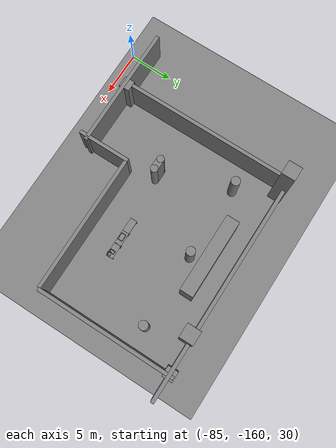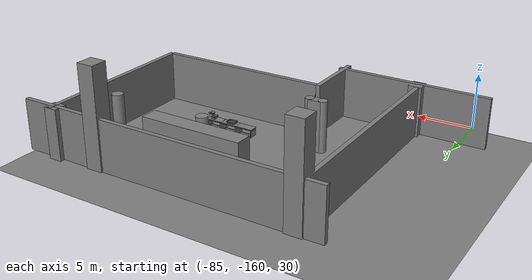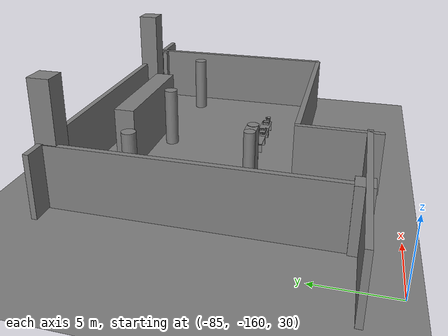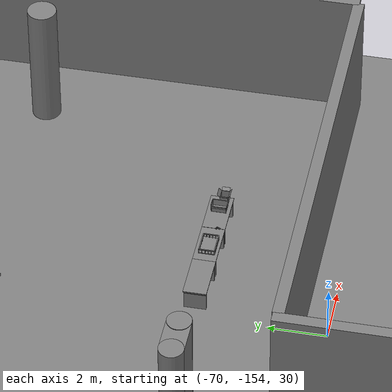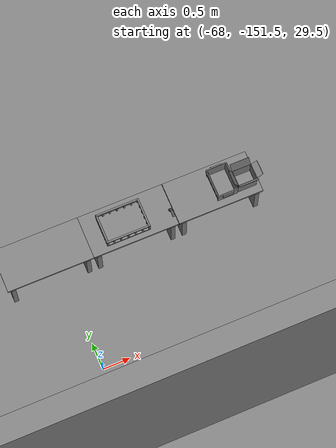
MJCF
<mujoco>
    <option gravity="0.000000000 0.000000000 -9.810000420" timestep="0.0049999999" integrator="implicitfast" density="1.225" viscosity="1.8000001e-05" noslip_iterations="10" iterations="100" sdf_iterations="50">
        <flag multiccd="disable"/>
    </option>
    <size memory="1000M"/>
    <compiler coordinate="local"/>
    <worldbody>
        <light cutoff="30" pos="0 1 1" dir="0 -1 -2"/>
        <light cutoff="30" pos="0 -1 1" dir="0 1 -2"/>
        <body pos="-64.866622925 -149.383972168 30.183746338" euler="89.999992371 89.999946594 0.000000000" name="openloong_gripper_2f85_fix_base_usda_bluebox_01">
            <geom contype="1" conaffinity="1" density="1000" type="box" material="" rgba="0.500000000 0.500000000 0.500000000 1.000000000" solimp="0.899999976 0.949999988 0.001000000" friction="1.000000000 0.005000000 0.000100000" solref="0.020000000 1.000000000" margin="0" condim="3" group="0" pos="0.276596069 0.187225342 0.000061035" quat="0.707107008 0.000077501 0.707106471 0.000077456" size="0.100000001 0.057999998 0.010000000" name="openloong_gripper_2f85_fix_base_usda_geom_B0467F13_7FFB_4F6E_B52F_C438FCC4DBFD"/>
            <geom contype="1" conaffinity="1" density="1000" type="box" material="" rgba="0.500000000 0.500000000 0.500000000 1.000000000" solimp="0.899999976 0.949999988 0.001000000" friction="1.000000000 0.005000000 0.000100000" solref="0.020000000 1.000000000" margin="0" condim="3" group="0" pos="0.000000000 0.002883911 0.000000000" quat="1.000000000 0.000000000 0.000000000 0.000000000" size="0.254000008 0.003000000 0.172000006" name="openloong_gripper_2f85_fix_base_usda_geom_D641A0BD_BB07_40F4_BA8A_1D166B5B7F34"/>
            <geom contype="1" conaffinity="1" density="1000" type="box" material="" rgba="0.500000000 0.500000000 0.500000000 1.000000000" solimp="0.899999976 0.949999988 0.001000000" friction="1.000000000 0.005000000 0.000100000" solref="0.020000000 1.000000000" margin="0" condim="3" group="0" pos="0.000015259 0.124874115 0.173477173" quat="0.999796450 0.020176515 -0.000000015 0.000000030" size="0.259999990 0.119999997 0.007000000" name="openloong_gripper_2f85_fix_base_usda_geom_D80B5C7F_8C4C_4E50_9028_EC7F0B8EF75A"/>
            <geom contype="1" conaffinity="1" density="1000" type="box" material="" rgba="0.500000000 0.500000000 0.500000000 1.000000000" solimp="0.899999976 0.949999988 0.001000000" friction="1.000000000 0.005000000 0.000100000" solref="0.020000000 1.000000000" margin="0" condim="3" group="0" pos="0.000015259 0.124874115 -0.173477173" quat="0.999796450 -0.020176545 -0.000000015 0.000000000" size="0.259999990 0.119999997 0.007000000" name="openloong_gripper_2f85_fix_base_usda_geom_7BA039A5_C27B_439B_849D_B682BA09B655"/>
            <geom contype="1" conaffinity="1" density="1000" type="box" material="" rgba="0.500000000 0.500000000 0.500000000 1.000000000" solimp="0.899999976 0.949999988 0.001000000" friction="1.000000000 0.005000000 0.000100000" solref="0.020000000 1.000000000" margin="0" condim="3" group="0" pos="0.000015259 0.214012146 0.188980103" quat="0.999913096 0.013176724 0.000000015 0.000000000" size="0.259999990 0.029999999 0.012500000" name="openloong_gripper_2f85_fix_base_usda_geom_6CEA2CBD_05B0_4EDC_AC3F_19AF47F8531B"/>
            <geom contype="1" conaffinity="1" density="1000" type="box" material="" rgba="0.500000000 0.500000000 0.500000000 1.000000000" solimp="0.899999976 0.949999988 0.001000000" friction="1.000000000 0.005000000 0.000100000" solref="0.020000000 1.000000000" margin="0" condim="3" group="0" pos="-0.258346558 0.125289917 0.001876831" quat="0.702796996 -0.020792052 0.710783184 0.020769238" size="0.189999998 0.119999997 0.009000000" name="openloong_gripper_2f85_fix_base_usda_geom_B8DC627C_731F_4BCD_B3D0_2814DAAD8D25"/>
            <geom contype="1" conaffinity="1" density="1000" type="box" material="" rgba="0.500000000 0.500000000 0.500000000 1.000000000" solimp="0.899999976 0.949999988 0.001000000" friction="1.000000000 0.005000000 0.000100000" solref="0.020000000 1.000000000" margin="0" condim="3" group="0" pos="0.000015259 0.214012146 -0.188980103" quat="0.999913096 -0.013176769 0.000000030 0.000000015" size="0.259999990 0.029999999 0.012500000" name="openloong_gripper_2f85_fix_base_usda_geom_2CFC2577_0623_47BF_958A_EEE21C8E35B5"/>
            <geom contype="1" conaffinity="1" density="1000" type="box" material="" rgba="0.500000000 0.500000000 0.500000000 1.000000000" solimp="0.899999976 0.949999988 0.001000000" friction="1.000000000 0.005000000 0.000100000" solref="0.020000000 1.000000000" margin="0" condim="3" group="0" pos="-0.276596069 0.187225342 0.000061035" quat="0.707106650 0.000077441 0.707106709 0.000077456" size="0.100000001 0.057999998 0.010000000" name="openloong_gripper_2f85_fix_base_usda_geom_1E6FF3E6_8258_4A5C_AF9A_79C70892510D"/>
            <geom contype="1" conaffinity="1" density="1000" type="box" material="" rgba="0.500000000 0.500000000 0.500000000 1.000000000" solimp="0.899999976 0.949999988 0.001000000" friction="1.000000000 0.005000000 0.000100000" solref="0.020000000 1.000000000" margin="0" condim="3" group="0" pos="0.258346558 0.125289917 0.001876831" quat="0.702851534 0.018856451 0.710823834 -0.019329429" size="0.189999998 0.119999997 0.009000000" name="openloong_gripper_2f85_fix_base_usda_geom_C226A567_A0C8_4864_8855_B9067E6023AF"/>
            <freejoint name="openloong_gripper_2f85_fix_base_usda_bluebox_01_joint"/>
            <site size="0.005000000 0.005000000 0.005000000" rgba="0.500000000 0.500000000 0.500000000 1.000000000" pos="0.000000000 0.000000000 0.000000000" quat="0.999961913 0.008726534 0.000000000 0.000000000" group="0" type="sphere" name="openloong_gripper_2f85_fix_base_usda_bluebox_01site"/>
        </body>
        <body pos="-64.496299744 -149.491867065 30.235729218" euler="0.000000000 0.000000000 89.999946594" name="openloong_gripper_2f85_fix_base_usda_cardboardbox_01">
            <geom contype="1" conaffinity="1" density="1000" type="box" material="" rgba="0.500000000 0.500000000 0.500000000 1.000000000" solimp="0.899999976 0.949999988 0.001000000" friction="1.000000000 0.005000000 0.000100000" solref="0.020000000 1.000000000" margin="0" condim="3" group="0" pos="-0.003166199 -0.004086494 0.005052090" quat="1.000000000 0.000000000 0.000000000 0.000000000" size="0.142499998 0.177500010 0.005000000" name="openloong_gripper_2f85_fix_base_usda_geom_74E2638B_B221_4EF2_9B91_00395A39041A"/>
            <geom contype="1" conaffinity="1" density="1000" type="box" material="" rgba="0.500000000 0.500000000 0.500000000 1.000000000" solimp="0.899999976 0.949999988 0.001000000" friction="1.000000000 0.005000000 0.000100000" solref="0.020000000 1.000000000" margin="0" condim="3" group="0" pos="-0.003166199 0.170316696 0.150570869" quat="1.000000000 0.000000000 0.000000000 0.000000000" size="0.142499998 0.005000000 0.149999991" name="openloong_gripper_2f85_fix_base_usda_geom_9712F9D0_17A9_40CA_B20F_53A8DBAEF85C"/>
            <geom contype="1" conaffinity="1" density="1000" type="box" material="" rgba="0.500000000 0.500000000 0.500000000 1.000000000" solimp="0.899999976 0.949999988 0.001000000" friction="1.000000000 0.005000000 0.000100000" solref="0.020000000 1.000000000" margin="0" condim="3" group="0" pos="-0.147399902 -0.005307198 0.150570869" quat="1.000000000 0.000000000 0.000000000 0.000000000" size="0.005000000 0.177500010 0.149999991" name="openloong_gripper_2f85_fix_base_usda_geom_7C7208E1_C3B1_4F36_A698_AFF5B7212FEB"/>
            <geom contype="1" conaffinity="1" density="1000" type="box" material="" rgba="0.500000000 0.500000000 0.500000000 1.000000000" solimp="0.899999976 0.949999988 0.001000000" friction="1.000000000 0.005000000 0.000100000" solref="0.020000000 1.000000000" margin="0" condim="3" group="0" pos="0.140275955 -0.005307198 0.150570869" quat="1.000000000 0.000000000 0.000000000 0.000000000" size="0.005000000 0.177500010 0.149999991" name="openloong_gripper_2f85_fix_base_usda_geom_E968E3F5_A152_4E3D_BDBE_E08ACA0FA28D"/>
            <geom contype="1" conaffinity="1" density="1000" type="box" material="" rgba="0.500000000 0.500000000 0.500000000 1.000000000" solimp="0.899999976 0.949999988 0.001000000" friction="1.000000000 0.005000000 0.000100000" solref="0.020000000 1.000000000" margin="0" condim="3" group="0" pos="-0.003166199 -0.181550980 0.150570869" quat="1.000000000 0.000000000 0.000000000 0.000000000" size="0.142499998 0.005000000 0.149999991" name="openloong_gripper_2f85_fix_base_usda_geom_038C3885_85C4_4300_B46D_B1DBA67FB21A"/>
            <freejoint name="openloong_gripper_2f85_fix_base_usda_cardboardbox_01_joint"/>
            <site size="0.005000000 0.005000000 0.005000000" rgba="0.500000000 0.500000000 0.500000000 1.000000000" pos="0.000000000 0.000000000 0.000000000" quat="0.999961913 0.008726535 0.000000000 0.000000000" group="0" type="sphere" name="openloong_gripper_2f85_fix_base_usda_site_823826DD_1D61_4C25_A594_0AD0B0A71A97"/>
            <body pos="0.139160156 -0.004048347 0.301930904" euler="-179.999954224 49.383502960 179.999954224" name="openloong_gripper_2f85_fix_base_usda_A1_006">
                <geom contype="1" conaffinity="1" density="1000" type="box" material="" rgba="0.500000000 0.500000000 0.500000000 1.000000000" solimp="0.899999976 0.949999988 0.001000000" friction="1.000000000 0.005000000 0.000100000" solref="0.020000000 1.000000000" margin="0" condim="3" group="0" pos="-0.071587563 0.000009537 0.001745224" quat="0.999999881 0.000000000 0.000000000 0.000000000" size="0.071249999 0.179999992 0.002500000" name="openloong_gripper_2f85_fix_base_usda_geom_A4FE2082_DDDE_44BC_B89D_D9DD16CE2A82"/>
                <joint armature="0" stiffness="0.07" damping="0.0099999998" axis="0.000000 1.000000 0.000000" type="hinge" name="openloong_gripper_2f85_fix_base_usda_A1_006"/>
            </body>
            <body pos="-0.145902634 -0.004086494 0.301938057" euler="-180.000000000 -60.000011444 -180.000000000" name="openloong_gripper_2f85_fix_base_usda_A2_006">
                <geom contype="1" conaffinity="1" density="1000" type="box" material="" rgba="0.500000000 0.500000000 0.500000000 1.000000000" solimp="0.899999976 0.949999988 0.001000000" friction="1.000000000 0.005000000 0.000100000" solref="0.020000000 1.000000000" margin="0" condim="3" group="0" pos="0.071268082 0.000009537 0.002717972" quat="0.000002921 0.000000000 -0.000000030 0.999999881" size="0.071249999 0.179999992 0.002500000" name="openloong_gripper_2f85_fix_base_usda_geom_A09F1ACB_7FE5_4F3B_B022_9E488C1AA983"/>
                <joint armature="0" stiffness="0.07" damping="0.0099999998" axis="0.000000 1.000000 0.000000" type="hinge" name="openloong_gripper_2f85_fix_base_usda_A2_006"/>
            </body>
            <body pos="-0.003385544 0.175991058 0.301930904" euler="-125.858116150 -0.000004561 0.000002331" name="openloong_gripper_2f85_fix_base_usda_B2_006">
                <geom contype="1" conaffinity="1" density="1000" type="box" material="" rgba="0.500000000 0.500000000 0.500000000 1.000000000" solimp="0.899999976 0.949999988 0.001000000" friction="1.000000000 0.005000000 0.000100000" solref="0.020000000 1.000000000" margin="0" condim="3" group="0" pos="0.000009537 -0.070939064 -0.002470016" quat="0.999614120 0.027776197 -0.000000015 0.000000030" size="0.137500003 0.064999998 0.005000000" name="openloong_gripper_2f85_fix_base_usda_geom_CD944FBA_3987_4CD3_81A8_A5330C2D170F"/>
                <joint armature="0" stiffness="0.07" damping="0.0099999998" axis="1.000000 0.000000 0.000000" type="hinge" name="openloong_gripper_2f85_fix_base_usda_B2_006"/>
            </body>
            <body pos="-0.003385544 -0.184140205 0.301938057" euler="147.805557251 0.000000000 0.000000000" name="openloong_gripper_2f85_fix_base_usda_B1_006">
                <geom contype="1" conaffinity="1" density="1000" type="box" material="" rgba="0.500000000 0.500000000 0.500000000 1.000000000" solimp="0.899999976 0.949999988 0.001000000" friction="1.000000000 0.005000000 0.000100000" solref="0.020000000 1.000000000" margin="0" condim="3" group="0" pos="-0.000028610 0.070202351 -0.002703667" quat="0.999614179 -0.027776167 0.000000000 0.000000000" size="0.137500003 0.064999998 0.005000000" name="openloong_gripper_2f85_fix_base_usda_geom_187D8BC6_CA4E_4355_B4DB_A20ACCA49E99"/>
                <joint armature="0" stiffness="0.07" damping="0.0099999998" axis="1.000000 0.000000 0.000000" type="hinge" name="openloong_gripper_2f85_fix_base_usda_B1_006"/>
            </body>
        </body>
        <body pos="-65.882858276 -149.481979370 30.229999542" euler="-64.487716675 0.000000000 0.000000000" name="openloong_gripper_2f85_fix_base_usda_Barcode">
            <geom contype="1" conaffinity="1" density="1000" type="box" material="" rgba="0.500000000 0.500000000 0.500000000 1.000000000" solimp="0.899999976 0.949999988 0.001000000" friction="1.000000000 0.005000000 0.000100000" solref="0.020000000 1.000000000" margin="0" condim="3" group="0" pos="0.000000000 0.013038635 0.001419067" quat="0.000000000 0.000000000 0.000000000 1.000000119" size="0.034000002 0.010000000 0.017999999" name="openloong_gripper_2f85_fix_base_usda_geom_16FBE9B5_2524_466C_8AA2_AF4FB490854D"/>
            <geom contype="1" conaffinity="1" density="1000" type="box" material="" rgba="0.500000000 0.500000000 0.500000000 1.000000000" solimp="0.899999976 0.949999988 0.001000000" friction="1.000000000 0.005000000 0.000100000" solref="0.020000000 1.000000000" margin="0" condim="3" group="0" pos="0.000000000 -0.035301208 -0.007095337" quat="0.000000000 0.000000000 -0.043619365 0.999048233" size="0.028999999 0.010000000 0.020000000" name="openloong_gripper_2f85_fix_base_usda_geom_244A6D73_E033_4F69_ADE4_F37C725CA272"/>
            <geom contype="1" conaffinity="1" density="1000" type="box" material="" rgba="0.500000000 0.500000000 0.500000000 1.000000000" solimp="0.899999976 0.949999988 0.001000000" friction="1.000000000 0.005000000 0.000100000" solref="0.020000000 1.000000000" margin="0" condim="3" group="0" pos="0.000000000 -0.043411255 -0.011749268" quat="0.922262907 0.386563420 0.000000000 0.000000000" size="0.026000001 0.010000000 0.020000000" name="openloong_gripper_2f85_fix_base_usda_geom_85078A1E_6404_4423_9FB8_1EC76DF8AD86"/>
            <geom contype="1" conaffinity="1" density="1000" type="box" material="" rgba="0.500000000 0.500000000 0.500000000 1.000000000" solimp="0.899999976 0.949999988 0.001000000" friction="1.000000000 0.005000000 0.000100000" solref="0.020000000 1.000000000" margin="0" condim="3" group="0" pos="0.000000000 -0.016967773 -0.031860352" quat="0.000000000 0.000000000 0.000000000 1.000000119" size="0.008000000 0.010000000 0.013000000" name="openloong_gripper_2f85_fix_base_usda_geom_4478D498_84C0_4911_8F1A_11F556A7B23F"/>
            <geom contype="1" conaffinity="1" density="1000" type="box" material="" rgba="0.500000000 0.500000000 0.500000000 1.000000000" solimp="0.899999976 0.949999988 0.001000000" friction="1.000000000 0.005000000 0.000100000" solref="0.020000000 1.000000000" margin="0" condim="3" group="0" pos="0.000000000 -0.001869202 0.000312805" quat="0.953716993 0.300705761 0.000000000 0.000000000" size="0.032000002 0.010000000 0.018999999" name="openloong_gripper_2f85_fix_base_usda_geom_DB6DAD73_B80C_4CAB_9B50_A08BAD07C7D6"/>
            <geom contype="1" conaffinity="1" density="1000" type="box" material="" rgba="0.500000000 0.500000000 0.500000000 1.000000000" solimp="0.899999976 0.949999988 0.001000000" friction="1.000000000 0.005000000 0.000100000" solref="0.020000000 1.000000000" margin="0" condim="3" group="0" pos="0.000000000 -0.019531250 -0.003173828" quat="0.953716993 0.300705761 0.000000000 0.000000000" size="0.030999999 0.010000000 0.020000000" name="openloong_gripper_2f85_fix_base_usda_geom_E2CC5BED_11E2_4DED_B5EA_A998DBD8E58B"/>
            <geom contype="1" conaffinity="1" density="1000" type="box" material="" rgba="0.500000000 0.500000000 0.500000000 1.000000000" solimp="0.899999976 0.949999988 0.001000000" friction="1.000000000 0.005000000 0.000100000" solref="0.020000000 1.000000000" margin="0" condim="3" group="0" pos="0.000000000 -0.035301208 -0.007095337" quat="0.953716993 0.300705761 0.000000000 0.000000000" size="0.028999999 0.010000000 0.020000000" name="openloong_gripper_2f85_fix_base_usda_geom_5ADB9C65_2AA2_48F1_B5AA_D3B0FE5E7A54"/>
            <geom contype="1" conaffinity="1" density="1000" type="box" material="" rgba="0.500000000 0.500000000 0.500000000 1.000000000" solimp="0.899999976 0.949999988 0.001000000" friction="1.000000000 0.005000000 0.000100000" solref="0.020000000 1.000000000" margin="0" condim="3" group="0" pos="0.000000000 -0.042617798 -0.071121216" quat="0.000000000 0.000000000 0.000000000 1.000000119" size="0.013000000 0.021000000 0.059999999" name="openloong_gripper_2f85_fix_base_usda_geom_9861E0EB_A717_4B35_BDC6_29CAFD2CC743"/>
            <freejoint name="openloong_gripper_2f85_fix_base_usda_Barcode_joint"/>
            <site size="0.005000000 0.005000000 0.005000000" rgba="0.500000000 0.500000000 0.500000000 1.000000000" pos="0.000000000 0.000000000 0.000000000" quat="1.000000000 0.000000000 0.000000000 0.000000000" group="0" type="sphere" name="openloong_gripper_2f85_fix_base_usda_Barcode_site"/>
        </body>
        <body pos="-66.745018005 -149.392349243 30.184000015" euler="0.000000000 0.000000000 89.999946594" name="[22330204280575]_Basket_01">
            <geom contype="1" conaffinity="1" density="1000" type="box" material="" rgba="0.500000000 0.500000000 0.500000000 1.000000000" solimp="0.899999976 0.949999988 0.001000000" friction="1.000000000 0.005000000 0.000100000" solref="0.020000000 1.000000000" margin="0" condim="3" group="0" pos="-0.052425385 0.389207840 0.089787483" quat="0.707107008 0.000000000 0.000000000 0.707106411" size="0.014249999 0.014249999 0.059999999" name="[22330204280575]_geom_132367AB_3A70_49A9_85A6_879AC22FC5B5"/>
            <geom contype="1" conaffinity="1" density="1000" type="box" material="" rgba="0.500000000 0.500000000 0.500000000 1.000000000" solimp="0.899999976 0.949999988 0.001000000" friction="1.000000000 0.005000000 0.000100000" solref="0.020000000 1.000000000" margin="0" condim="3" group="0" pos="0.264015198 -0.133043289 0.089787483" quat="0.707107008 0.000000000 0.000000000 0.707106411" size="0.014249999 0.014249999 0.059999999" name="[22330204280575]_geom_FAD8F9A9_8CCE_4B49_8782_15E8CF89EC19"/>
            <geom contype="1" conaffinity="1" density="1000" type="box" material="" rgba="0.500000000 0.500000000 0.500000000 1.000000000" solimp="0.899999976 0.949999988 0.001000000" friction="1.000000000 0.005000000 0.000100000" solref="0.020000000 1.000000000" margin="0" condim="3" group="0" pos="-0.264015198 -0.265548706 0.089793205" quat="0.707107008 0.000000000 0.000000000 0.707106411" size="0.014249999 0.014249999 0.059999999" name="[22330204280575]_geom_5BAB52F2_5547_42C1_9DCB_3AF4B5B6C5EF"/>
            <geom contype="1" conaffinity="1" density="1000" type="box" material="" rgba="0.500000000 0.500000000 0.500000000 1.000000000" solimp="0.899999976 0.949999988 0.001000000" friction="1.000000000 0.005000000 0.000100000" solref="0.020000000 1.000000000" margin="0" condim="3" group="0" pos="-0.160263062 -0.389322281 0.089793205" quat="0.707107008 0.000000000 0.000000000 0.707106411" size="0.014249999 0.014249999 0.059999999" name="[22330204280575]_geom_8044373F_652C_4FA3_AF3E_1A9F9DEB0B40"/>
            <geom contype="1" conaffinity="1" density="1000" type="box" material="" rgba="0.500000000 0.500000000 0.500000000 1.000000000" solimp="0.899999976 0.949999988 0.001000000" friction="1.000000000 0.005000000 0.000100000" solref="0.020000000 1.000000000" margin="0" condim="3" group="0" pos="0.162265778 -0.389322281 0.089787483" quat="0.707107008 0.000000000 0.000000000 0.707106411" size="0.014249999 0.014249999 0.059999999" name="[22330204280575]_geom_F89FC73F_591B_49BE_BCEB_B3267EA8F373"/>
            <geom contype="1" conaffinity="1" density="1000" type="box" material="" rgba="0.500000000 0.500000000 0.500000000 1.000000000" solimp="0.899999976 0.949999988 0.001000000" friction="1.000000000 0.005000000 0.000100000" solref="0.020000000 1.000000000" margin="0" condim="3" group="0" pos="0.264015198 0.389207840 0.089787483" quat="0.707107008 0.000000000 0.000000000 0.707106411" size="0.014249999 0.014249999 0.059999999" name="[22330204280575]_geom_AA4BAA25_3FEB_4F1C_82D8_B412196811BD"/>
            <geom contype="1" conaffinity="1" density="1000" type="box" material="" rgba="0.500000000 0.500000000 0.500000000 1.000000000" solimp="0.899999976 0.949999988 0.001000000" friction="1.000000000 0.005000000 0.000100000" solref="0.020000000 1.000000000" margin="0" condim="3" group="0" pos="-0.264015198 -0.133043289 0.089793205" quat="0.707107008 0.000000000 0.000000000 0.707106411" size="0.014249999 0.014249999 0.059999999" name="[22330204280575]_geom_50A7DFC4_4B6A_4499_B3C1_13173E3E2031"/>
            <geom contype="1" conaffinity="1" density="1000" type="box" material="" rgba="0.500000000 0.500000000 0.500000000 1.000000000" solimp="0.899999976 0.949999988 0.001000000" friction="1.000000000 0.005000000 0.000100000" solref="0.020000000 1.000000000" margin="0" condim="3" group="0" pos="-0.264026642 0.269256592 0.089793205" quat="0.707107008 0.000000000 0.000000000 0.707106411" size="0.014249999 0.014249999 0.059999999" name="[22330204280575]_geom_A0A4B109_EB6E_4195_B583_41154AA6816C"/>
            <geom contype="1" conaffinity="1" density="1000" type="box" material="" rgba="0.500000000 0.500000000 0.500000000 1.000000000" solimp="0.899999976 0.949999988 0.001000000" friction="1.000000000 0.005000000 0.000100000" solref="0.020000000 1.000000000" margin="0" condim="3" group="0" pos="0.054462433 0.389207840 0.089787483" quat="0.707107008 0.000000000 0.000000000 0.707106411" size="0.014249999 0.014249999 0.059999999" name="[22330204280575]_geom_06DE3D50_609F_4932_91D8_123261913E80"/>
            <geom contype="1" conaffinity="1" density="1000" type="box" material="" rgba="0.500000000 0.500000000 0.500000000 1.000000000" solimp="0.899999976 0.949999988 0.001000000" friction="1.000000000 0.005000000 0.000100000" solref="0.020000000 1.000000000" margin="0" condim="3" group="0" pos="0.054462433 -0.389322281 0.089787483" quat="0.707107008 0.000000000 0.000000000 0.707106411" size="0.014249999 0.014249999 0.059999999" name="[22330204280575]_geom_0E511A16_F1D8_4B8F_BB6D_55D6753920E6"/>
            <geom contype="1" conaffinity="1" density="1000" type="box" material="" rgba="0.500000000 0.500000000 0.500000000 1.000000000" solimp="0.899999976 0.949999988 0.001000000" friction="1.000000000 0.005000000 0.000100000" solref="0.020000000 1.000000000" margin="0" condim="3" group="0" pos="0.264015198 0.269256592 0.089793205" quat="0.707107008 0.000000000 0.000000000 0.707106411" size="0.014249999 0.014249999 0.059999999" name="[22330204280575]_geom_FC4BEF3B_0180_444C_931B_145653D6A613"/>
            <geom contype="1" conaffinity="1" density="1000" type="box" material="" rgba="0.500000000 0.500000000 0.500000000 1.000000000" solimp="0.899999976 0.949999988 0.001000000" friction="1.000000000 0.005000000 0.000100000" solref="0.020000000 1.000000000" margin="0" condim="3" group="0" pos="0.264015198 -0.389322281 0.089787483" quat="0.707107008 0.000000000 0.000000000 0.707106411" size="0.014249999 0.014249999 0.059999999" name="[22330204280575]_geom_8722E589_4123_4B03_ACA6_1E17D6267D6C"/>
            <geom contype="1" conaffinity="1" density="1000" type="box" material="" rgba="0.500000000 0.500000000 0.500000000 1.000000000" solimp="0.899999976 0.949999988 0.001000000" friction="1.000000000 0.005000000 0.000100000" solref="0.020000000 1.000000000" margin="0" condim="3" group="0" pos="0.000000000 0.000000000 0.015998840" quat="0.707107008 0.000000000 0.000000000 0.707106411" size="0.403499991 0.279000014 0.015750000" name="[22330204280575]_geom_E77FD9D7_DC72_4852_B7A7_B1C5B2FC40AE"/>
            <geom contype="1" conaffinity="1" density="1000" type="box" material="" rgba="0.500000000 0.500000000 0.500000000 1.000000000" solimp="0.899999976 0.949999988 0.001000000" friction="1.000000000 0.005000000 0.000100000" solref="0.020000000 1.000000000" margin="0" condim="3" group="0" pos="0.000000000 -0.389476776 0.163619041" quat="0.707107008 0.000000000 0.000000000 0.707106411" size="0.015000000 0.277500004 0.015750000" name="[22330204280575]_geom_10CCF51B_370B_40CC_8404_AF68AD82C314"/>
            <geom contype="1" conaffinity="1" density="1000" type="box" material="" rgba="0.500000000 0.500000000 0.500000000 1.000000000" solimp="0.899999976 0.949999988 0.001000000" friction="1.000000000 0.005000000 0.000100000" solref="0.020000000 1.000000000" margin="0" condim="3" group="0" pos="0.162265778 0.389207840 0.089787483" quat="0.707107008 0.000000000 0.000000000 0.707106411" size="0.014249999 0.014249999 0.059999999" name="[22330204280575]_geom_289D7B11_5AE2_4F81_8E9D_D4B6440ADB39"/>
            <geom contype="1" conaffinity="1" density="1000" type="box" material="" rgba="0.500000000 0.500000000 0.500000000 1.000000000" solimp="0.899999976 0.949999988 0.001000000" friction="1.000000000 0.005000000 0.000100000" solref="0.020000000 1.000000000" margin="0" condim="3" group="0" pos="0.000000000 0.389471054 0.163619041" quat="0.707107008 0.000000000 0.000000000 0.707106411" size="0.015000000 0.277500004 0.015750000" name="[22330204280575]_geom_B545660E_D4C2_45BF_81D1_101B9D89FD43"/>
            <geom contype="1" conaffinity="1" density="1000" type="box" material="" rgba="0.500000000 0.500000000 0.500000000 1.000000000" solimp="0.899999976 0.949999988 0.001000000" friction="1.000000000 0.005000000 0.000100000" solref="0.020000000 1.000000000" margin="0" condim="3" group="0" pos="-0.263511658 0.000000000 0.163619041" quat="0.707107008 0.000000000 0.000000000 0.707106411" size="0.403499991 0.015000000 0.015750000" name="[22330204280575]_geom_8A34C10E_AEF2_4271_809E_376C85F4880E"/>
            <geom contype="1" conaffinity="1" density="1000" type="box" material="" rgba="0.500000000 0.500000000 0.500000000 1.000000000" solimp="0.899999976 0.949999988 0.001000000" friction="1.000000000 0.005000000 0.000100000" solref="0.020000000 1.000000000" margin="0" condim="3" group="0" pos="-0.264015198 0.141334534 0.089793205" quat="0.707107008 0.000000000 0.000000000 0.707106411" size="0.014249999 0.014249999 0.059999999" name="[22330204280575]_geom_6235BE7B_222D_4EEA_A339_1887FB9824A8"/>
            <geom contype="1" conaffinity="1" density="1000" type="box" material="" rgba="0.500000000 0.500000000 0.500000000 1.000000000" solimp="0.899999976 0.949999988 0.001000000" friction="1.000000000 0.005000000 0.000100000" solref="0.020000000 1.000000000" margin="0" condim="3" group="0" pos="0.264015198 -0.265548706 0.089787483" quat="0.707107008 0.000000000 0.000000000 0.707106411" size="0.014249999 0.014249999 0.059999999" name="[22330204280575]_geom_90D4E4A7_334F_40B9_A8B8_A01691491133"/>
            <geom contype="1" conaffinity="1" density="1000" type="box" material="" rgba="0.500000000 0.500000000 0.500000000 1.000000000" solimp="0.899999976 0.949999988 0.001000000" friction="1.000000000 0.005000000 0.000100000" solref="0.020000000 1.000000000" margin="0" condim="3" group="0" pos="-0.160263062 0.389207840 0.089787483" quat="0.707107008 0.000000000 0.000000000 0.707106411" size="0.014249999 0.014249999 0.059999999" name="[22330204280575]_geom_E0B6F366_279F_426C_9B0C_18E4A28ECF6B"/>
            <geom contype="1" conaffinity="1" density="1000" type="box" material="" rgba="0.500000000 0.500000000 0.500000000 1.000000000" solimp="0.899999976 0.949999988 0.001000000" friction="1.000000000 0.005000000 0.000100000" solref="0.020000000 1.000000000" margin="0" condim="3" group="0" pos="-0.052425385 -0.389322281 0.089787483" quat="0.707107008 0.000000000 0.000000000 0.707106411" size="0.014249999 0.014249999 0.059999999" name="[22330204280575]_geom_F7C6D9D5_FF79_464F_A4ED_D17788F9207B"/>
            <geom contype="1" conaffinity="1" density="1000" type="box" material="" rgba="0.500000000 0.500000000 0.500000000 1.000000000" solimp="0.899999976 0.949999988 0.001000000" friction="1.000000000 0.005000000 0.000100000" solref="0.020000000 1.000000000" margin="0" condim="3" group="0" pos="-0.264026642 -0.389322281 0.089793205" quat="0.707107008 0.000000000 0.000000000 0.707106411" size="0.014249999 0.014249999 0.059999999" name="[22330204280575]_geom_8A26C7B0_ECCA_4B62_9133_3B42959C963B"/>
            <geom contype="1" conaffinity="1" density="1000" type="box" material="" rgba="0.500000000 0.500000000 0.500000000 1.000000000" solimp="0.899999976 0.949999988 0.001000000" friction="1.000000000 0.005000000 0.000100000" solref="0.020000000 1.000000000" margin="0" condim="3" group="0" pos="0.264015198 0.141334534 0.089787483" quat="0.707107008 0.000000000 0.000000000 0.707106411" size="0.014249999 0.014249999 0.059999999" name="[22330204280575]_geom_7E221A31_85E4_49EE_9E37_B6AB8656C208"/>
            <geom contype="1" conaffinity="1" density="1000" type="box" material="" rgba="0.500000000 0.500000000 0.500000000 1.000000000" solimp="0.899999976 0.949999988 0.001000000" friction="1.000000000 0.005000000 0.000100000" solref="0.020000000 1.000000000" margin="0" condim="3" group="0" pos="-0.264015198 0.389207840 0.089793205" quat="0.707107008 0.000000000 0.000000000 0.707106411" size="0.014249999 0.014249999 0.059999999" name="[22330204280575]_geom_CFA2F66B_B460_42D3_8AAD_00BE9E41620E"/>
            <geom contype="1" conaffinity="1" density="1000" type="box" material="" rgba="0.500000000 0.500000000 0.500000000 1.000000000" solimp="0.899999976 0.949999988 0.001000000" friction="1.000000000 0.005000000 0.000100000" solref="0.020000000 1.000000000" margin="0" condim="3" group="0" pos="0.264015198 0.004480362 0.089787483" quat="0.707107008 0.000000000 0.000000000 0.707106411" size="0.014249999 0.014249999 0.059999999" name="[22330204280575]_geom_E9C896AC_BF8F_4A26_9DA6_57067DED17EF"/>
            <geom contype="1" conaffinity="1" density="1000" type="box" material="" rgba="0.500000000 0.500000000 0.500000000 1.000000000" solimp="0.899999976 0.949999988 0.001000000" friction="1.000000000 0.005000000 0.000100000" solref="0.020000000 1.000000000" margin="0" condim="3" group="0" pos="0.263694763 -0.000011444 0.163619041" quat="0.707107008 0.000000000 0.000000000 0.707106411" size="0.403499991 0.015000000 0.015750000" name="[22330204280575]_geom_1463CEAE_B45C_4D2C_B413_7D7DCDC99911"/>
            <geom contype="1" conaffinity="1" density="1000" type="box" material="" rgba="0.500000000 0.500000000 0.500000000 1.000000000" solimp="0.899999976 0.949999988 0.001000000" friction="1.000000000 0.005000000 0.000100000" solref="0.020000000 1.000000000" margin="0" condim="3" group="0" pos="-0.264015198 0.004480362 0.089793205" quat="0.707107008 0.000000000 0.000000000 0.707106411" size="0.014249999 0.014249999 0.059999999" name="[22330204280575]_geom_2AF8E627_8548_4035_94E7_B4736DA4937B"/>
            <freejoint name="[22330204280575]_joint_8BE23A7E_92E5_4458_A272_5209A30DFA28"/>
        </body>
        <body pos="0.000000000 0.000000000 0.000000000" euler="0.000000000 0.000000000 0.000000000" name="Static Objects_Static Objects">
            <geom contype="1" conaffinity="1" density="1000" type="box" material="" rgba="0.500000000 0.500000000 0.500000000 1.000000000" solimp="0.899999976 0.949999988 0.001000000" friction="1.000000000 0.005000000 0.000100000" solref="0.020000000 1.000000000" margin="0" condim="3" group="0" pos="-67.544113159 -149.365814209 29.727830887" quat="0.500000417 0.499999970 0.499999553 0.499999970" size="0.381000012 0.319999993 0.041000001" name="Static Objects_geom_20C54981_E5E4_4647_AD59_45A89F70FFB8"/>
            <geom contype="1" conaffinity="1" density="1000" type="box" material="" rgba="0.500000000 0.500000000 0.500000000 1.000000000" solimp="0.899999976 0.949999988 0.001000000" friction="1.000000000 0.005000000 0.000100000" solref="0.020000000 1.000000000" margin="0" condim="3" group="0" pos="-68.239501953 -149.365814209 30.086868286" quat="0.500000417 0.499999970 0.499999553 0.499999970" size="0.370999992 0.039500002 0.745000005" name="Static Objects_geom_7DCDE875_397D_4281_8D3D_AB6C8DC0E91C"/>
            <geom contype="1" conaffinity="1" density="1000" type="box" material="" rgba="0.500000000 0.500000000 0.500000000 1.000000000" solimp="0.899999976 0.949999988 0.001000000" friction="1.000000000 0.005000000 0.000100000" solref="0.020000000 1.000000000" margin="0" condim="3" group="0" pos="-68.239501953 -149.365814209 30.147235870" quat="0.500000417 0.499999970 0.499999553 0.499999970" size="0.400000006 0.022000000 0.800000012" name="Static Objects_geom_8D8611D0_5C67_4929_88C2_FCE7ABC4C68D"/>
            <geom contype="1" conaffinity="1" density="1000" type="box" material="" rgba="0.500000000 0.500000000 0.500000000 1.000000000" solimp="0.899999976 0.949999988 0.001000000" friction="1.000000000 0.005000000 0.000100000" solref="0.020000000 1.000000000" margin="0" condim="3" group="0" pos="-68.934890747 -149.365814209 29.727830887" quat="0.500000417 0.499999970 0.499999553 0.499999970" size="0.381000012 0.319999993 0.041000001" name="Static Objects_geom_B5A3C3F3_067C_4791_9A26_40E3966C906A"/>
            <geom contype="1" conaffinity="1" density="1000" type="box" material="" rgba="0.500000000 0.500000000 0.500000000 1.000000000" solimp="0.899999976 0.949999988 0.001000000" friction="1.000000000 0.005000000 0.000100000" solref="0.020000000 1.000000000" margin="0" condim="3" group="0" pos="-68.239501953 -149.365814209 29.561563492" quat="0.500000417 0.499999970 0.499999553 0.499999970" size="0.020000000 0.022000000 0.660000026" name="Static Objects_geom_CB4F2241_99CA_438D_BCA3_93D93D3D48EB"/>
            <geom contype="1" conaffinity="1" density="1000" type="box" material="" rgba="0.500000000 0.500000000 0.500000000 1.000000000" solimp="0.899999976 0.949999988 0.001000000" friction="1.000000000 0.005000000 0.000100000" solref="0.020000000 1.000000000" margin="0" condim="3" group="0" pos="-65.945671082 -149.365814209 29.727830887" quat="0.500000417 0.499999970 0.499999553 0.499999970" size="0.381000012 0.319999993 0.041000001" name="Static Objects_geom_8A06C720_8902_4C78_BEE5_ABAA5237E4B6"/>
            <geom contype="1" conaffinity="1" density="1000" type="box" material="" rgba="0.500000000 0.500000000 0.500000000 1.000000000" solimp="0.899999976 0.949999988 0.001000000" friction="1.000000000 0.005000000 0.000100000" solref="0.020000000 1.000000000" margin="0" condim="3" group="0" pos="-66.641059875 -149.365814209 30.086868286" quat="0.500000417 0.499999970 0.499999553 0.499999970" size="0.370999992 0.039500002 0.745000005" name="Static Objects_geom_BED1EE34_3144_4FFA_BBF7_B72FD8008DE2"/>
            <geom contype="1" conaffinity="1" density="1000" type="box" material="" rgba="0.500000000 0.500000000 0.500000000 1.000000000" solimp="0.899999976 0.949999988 0.001000000" friction="1.000000000 0.005000000 0.000100000" solref="0.020000000 1.000000000" margin="0" condim="3" group="0" pos="-66.641059875 -149.365814209 30.147235870" quat="0.500000417 0.499999970 0.499999553 0.499999970" size="0.400000006 0.022000000 0.800000012" name="Static Objects_geom_2A0FA659_8002_4F66_A850_C44868A6A603"/>
            <geom contype="1" conaffinity="1" density="1000" type="box" material="" rgba="0.500000000 0.500000000 0.500000000 1.000000000" solimp="0.899999976 0.949999988 0.001000000" friction="1.000000000 0.005000000 0.000100000" solref="0.020000000 1.000000000" margin="0" condim="3" group="0" pos="-67.336448669 -149.365814209 29.727830887" quat="0.500000417 0.499999970 0.499999553 0.499999970" size="0.381000012 0.319999993 0.041000001" name="Static Objects_geom_06AEF93A_4F31_44BE_8FB4_5BEB482F31F0"/>
            <geom contype="1" conaffinity="1" density="1000" type="box" material="" rgba="0.500000000 0.500000000 0.500000000 1.000000000" solimp="0.899999976 0.949999988 0.001000000" friction="1.000000000 0.005000000 0.000100000" solref="0.020000000 1.000000000" margin="0" condim="3" group="0" pos="-66.641059875 -149.365814209 29.561563492" quat="0.500000417 0.499999970 0.499999553 0.499999970" size="0.020000000 0.022000000 0.660000026" name="Static Objects_geom_02072663_DD44_4C7D_BDAB_C18A5F49C6DD"/>
            <geom contype="1" conaffinity="1" density="1000" type="box" material="" rgba="0.500000000 0.500000000 0.500000000 1.000000000" solimp="0.899999976 0.949999988 0.001000000" friction="1.000000000 0.005000000 0.000100000" solref="0.020000000 1.000000000" margin="0" condim="3" group="0" pos="-64.338577271 -149.365814209 29.727830887" quat="0.500000417 0.499999970 0.499999553 0.499999970" size="0.381000012 0.319999993 0.041000001" name="Static Objects_geom_A3AB7346_5C75_4AF5_BBA2_930187ED6F3B"/>
            <geom contype="1" conaffinity="1" density="1000" type="box" material="" rgba="0.500000000 0.500000000 0.500000000 1.000000000" solimp="0.899999976 0.949999988 0.001000000" friction="1.000000000 0.005000000 0.000100000" solref="0.020000000 1.000000000" margin="0" condim="3" group="0" pos="-65.033966064 -149.365814209 30.086868286" quat="0.500000417 0.499999970 0.499999553 0.499999970" size="0.370999992 0.039500002 0.745000005" name="Static Objects_geom_947E93CD_7846_4762_BFE7_7BB2C70546C3"/>
            <geom contype="1" conaffinity="1" density="1000" type="box" material="" rgba="0.500000000 0.500000000 0.500000000 1.000000000" solimp="0.899999976 0.949999988 0.001000000" friction="1.000000000 0.005000000 0.000100000" solref="0.020000000 1.000000000" margin="0" condim="3" group="0" pos="-65.033966064 -149.365814209 30.147235870" quat="0.500000417 0.499999970 0.499999553 0.499999970" size="0.400000006 0.022000000 0.800000012" name="Static Objects_geom_DD81EF2E_D5E7_4B4A_8CAC_E4F3BDC4F604"/>
            <geom contype="1" conaffinity="1" density="1000" type="box" material="" rgba="0.500000000 0.500000000 0.500000000 1.000000000" solimp="0.899999976 0.949999988 0.001000000" friction="1.000000000 0.005000000 0.000100000" solref="0.020000000 1.000000000" margin="0" condim="3" group="0" pos="-65.729354858 -149.365814209 29.727830887" quat="0.500000417 0.499999970 0.499999553 0.499999970" size="0.381000012 0.319999993 0.041000001" name="Static Objects_geom_CB755A24_7C45_413A_B8B6_C62A5100768D"/>
            <geom contype="1" conaffinity="1" density="1000" type="box" material="" rgba="0.500000000 0.500000000 0.500000000 1.000000000" solimp="0.899999976 0.949999988 0.001000000" friction="1.000000000 0.005000000 0.000100000" solref="0.020000000 1.000000000" margin="0" condim="3" group="0" pos="-65.033966064 -149.365814209 29.561563492" quat="0.500000417 0.499999970 0.499999553 0.499999970" size="0.020000000 0.022000000 0.660000026" name="Static Objects_geom_84685A74_015F_43FA_8BCB_423125B0D5E7"/>
            <geom contype="1" conaffinity="1" density="1000" type="box" material="" rgba="0.500000000 0.500000000 0.500000000 1.000000000" solimp="0.899999976 0.949999988 0.001000000" friction="1.000000000 0.005000000 0.000100000" solref="0.020000000 1.000000000" margin="0" condim="3" group="0" pos="-61.754566193 -137.853729248 33.906845093" quat="0.707107067 0.000000000 0.000000000 0.707106471" size="0.759999990 0.759999990 4.500000000" name="Static Objects_geom_25FE8D1B_3D2F_4644_B15B_2A8E3330079F"/>
            <geom contype="1" conaffinity="1" density="1000" type="box" material="" rgba="0.500000000 0.500000000 0.500000000 1.000000000" solimp="0.899999976 0.949999988 0.001000000" friction="1.000000000 0.005000000 0.000100000" solref="0.020000000 1.000000000" margin="0" condim="3" group="0" pos="-57.511135101 -144.927108765 31.707921982" quat="1.000000000 0.000000000 0.000000000 0.000000000" size="0.200000003 8.000000000 2.299999952" name="Static Objects_geom_D7273C4D_0BE6_47FC_8BFF_3E960B078197"/>
            <geom contype="1" conaffinity="1" density="1000" type="box" material="" rgba="0.500000000 0.500000000 0.500000000 1.000000000" solimp="0.899999976 0.949999988 0.001000000" friction="1.000000000 0.005000000 0.000100000" solref="0.020000000 1.000000000" margin="0" condim="3" group="0" pos="-80.517646790 -157.574050903 31.688196182" quat="0.707107067 0.000000000 0.000000000 0.707106471" size="0.600000024 0.600000024 2.299999952" name="Static Objects_geom_B26A1DF5_8492_49E7_8978_76632FC4CFBC"/>
            <geom contype="1" conaffinity="1" density="1000" type="box" material="" rgba="0.500000000 0.500000000 0.500000000 1.000000000" solimp="0.899999976 0.949999988 0.001000000" friction="1.000000000 0.005000000 0.000100000" solref="0.020000000 1.000000000" margin="0" condim="3" group="0" pos="-80.711044312 -147.414932251 31.666158676" quat="1.000000000 0.000000000 0.000000000 0.000000000" size="0.200000003 10.000000000 2.299999952" name="Static Objects_geom_0A18BB5F_62A1_46D4_8D04_5AA6AF78E75D"/>
            <geom contype="1" conaffinity="1" density="1000" type="box" material="" rgba="0.500000000 0.500000000 0.500000000 1.000000000" solimp="0.899999976 0.949999988 0.001000000" friction="1.000000000 0.005000000 0.000100000" solref="0.020000000 1.000000000" margin="0" condim="3" group="0" pos="-57.687217712 -137.434692383 31.688196182" quat="0.707107067 0.000000000 0.000000000 0.707106471" size="0.600000024 0.600000024 2.299999952" name="Static Objects_geom_7011C323_79FA_4453_91ED_B4AABDFDE3AE"/>
            <geom contype="1" conaffinity="1" density="1000" type="box" material="" rgba="0.500000000 0.500000000 0.500000000 1.000000000" solimp="0.899999976 0.949999988 0.001000000" friction="1.000000000 0.005000000 0.000100000" solref="0.020000000 1.000000000" margin="0" condim="3" group="0" pos="-69.537033081 -140.263229370 31.714921951" quat="0.707107067 0.000000000 0.000000000 0.707106471" size="0.759999990 4.500000000 2.299999952" name="Static Objects_geom_33B3F77E_8FD7_44C6_8D5C_E51BCD4C5E6D"/>
            <geom contype="1" conaffinity="1" density="1000" type="box" material="" rgba="0.500000000 0.500000000 0.500000000 1.000000000" solimp="0.899999976 0.949999988 0.001000000" friction="1.000000000 0.005000000 0.000100000" solref="0.020000000 1.000000000" margin="0" condim="3" group="0" pos="-80.073638916 -137.853713989 33.906845093" quat="0.707107067 0.000000000 0.000000000 0.707106471" size="0.759999990 0.759999990 4.500000000" name="Static Objects_geom_3284EF2E_08DB_4DA7_8758_BFCB3D5F1815"/>
            <geom contype="1" conaffinity="1" density="1000" type="box" material="" rgba="0.500000000 0.500000000 0.500000000 1.000000000" solimp="0.899999976 0.949999988 0.001000000" friction="1.000000000 0.005000000 0.000100000" solref="0.020000000 1.000000000" margin="0" condim="3" group="0" pos="-73.406707764 -155.734664917 31.707921982" quat="1.000000000 0.000000000 0.000000000 0.000000000" size="0.200000003 3.000000000 2.299999952" name="Static Objects_geom_3971E854_64FE_4242_AF73_96C9ABA62993"/>
            <geom contype="1" conaffinity="1" density="1000" type="box" material="" rgba="0.500000000 0.500000000 0.500000000 1.000000000" solimp="0.899999976 0.949999988 0.001000000" friction="1.000000000 0.005000000 0.000100000" solref="0.020000000 1.000000000" margin="0" condim="3" group="0" pos="-68.497543335 -137.448257446 31.707921982" quat="0.707107067 0.000000000 0.000000000 0.707106471" size="0.200000003 14.000000000 2.299999952" name="Static Objects_geom_F84D8460_B002_4F07_995C_550CF56731E4"/>
            <geom contype="1" conaffinity="1" density="1000" type="cylinder" material="" rgba="0.500000000 0.500000000 0.500000000 1.000000000" solimp="0.899999976 0.949999988 0.001000000" friction="1.000000000 0.005000000 0.000100000" solref="0.020000000 1.000000000" margin="0" condim="3" group="0" pos="-68.868522644 -142.134506226 31.711090088" quat="0.707107067 0.000000000 0.000000000 0.707106471" size="0.509999990 2.299999952 1.000000000" name="Static Objects_geom_761FC950_51A5_45F4_B596_83CA7D1FC1BB"/>
            <geom contype="1" conaffinity="1" density="1000" type="plane" material="" rgba="0.500000000 0.500000000 0.500000000 1.000000000" solimp="0.899999976 0.949999988 0.001000000" friction="1.000000000 0.005000000 0.000100000" solref="0.020000000 1.000000000" margin="0" condim="3" group="0" pos="-72.873703003 -147.131927490 29.409669876" quat="1.000000000 0.000000000 0.000000000 0.000000000" size="18.000000000 14.000000000 1.000000000" name="Static Objects_geom_ECCA4D91_7AA1_47D6_BC5E_1A2313814CF7"/>
            <geom contype="1" conaffinity="1" density="1000" type="box" material="" rgba="0.500000000 0.500000000 0.500000000 1.000000000" solimp="0.899999976 0.949999988 0.001000000" friction="1.000000000 0.005000000 0.000100000" solref="0.020000000 1.000000000" margin="0" condim="3" group="0" pos="-79.943580627 -157.782272339 31.707921982" quat="0.707107067 0.000000000 0.000000000 0.707106471" size="0.200000003 7.000000000 2.299999952" name="Static Objects_geom_63318B23_0E95_42C2_BE3D_F79B7725B2DA"/>
            <geom contype="1" conaffinity="1" density="1000" type="box" material="" rgba="0.500000000 0.500000000 0.500000000 1.000000000" solimp="0.899999976 0.949999988 0.001000000" friction="1.000000000 0.005000000 0.000100000" solref="0.020000000 1.000000000" margin="0" condim="3" group="0" pos="-65.421028137 -152.903442383 31.707921982" quat="0.707107067 0.000000000 0.000000000 0.707106471" size="0.200000003 7.800000191 2.299999952" name="Static Objects_geom_E2508B79_A084_45F0_9354_A5DFBFA44450"/>
            <geom contype="1" conaffinity="1" density="1000" type="box" material="" rgba="0.500000000 0.500000000 0.500000000 1.000000000" solimp="0.899999976 0.949999988 0.001000000" friction="1.000000000 0.005000000 0.000100000" solref="0.020000000 1.000000000" margin="0" condim="3" group="0" pos="-74.776908875 -149.964416504 31.688196182" quat="1.000000000 0.000000000 0.000000000 0.000000000" size="0.600000024 0.409999996 2.299999952" name="Static Objects_geom_39B26F5E_E39E_4E63_8ABB_27E90E4AEAA6"/>
            <geom contype="1" conaffinity="1" density="1000" type="cylinder" material="" rgba="0.500000000 0.500000000 0.500000000 1.000000000" solimp="0.899999976 0.949999988 0.001000000" friction="1.000000000 0.005000000 0.000100000" solref="0.020000000 1.000000000" margin="0" condim="3" group="0" pos="-60.161884308 -142.134506226 31.711090088" quat="0.707107067 0.000000000 0.000000000 0.707106471" size="0.509999990 2.299999952 1.000000000" name="Static Objects_geom_9F186826_14B9_4A7A_8CEA_0D5497DDAB56"/>
            <geom contype="1" conaffinity="1" density="1000" type="cylinder" material="" rgba="0.500000000 0.500000000 0.500000000 1.000000000" solimp="0.899999976 0.949999988 0.001000000" friction="1.000000000 0.005000000 0.000100000" solref="0.020000000 1.000000000" margin="0" condim="3" group="0" pos="-75.382453918 -149.963455200 31.711090088" quat="0.707107067 0.000000000 0.000000000 0.707106471" size="0.409999996 2.299999952 1.000000000" name="Static Objects_geom_143604B0_E063_42DC_B0CF_4A29DE38B3B8"/>
            <geom contype="1" conaffinity="1" density="1000" type="cylinder" material="" rgba="0.500000000 0.500000000 0.500000000 1.000000000" solimp="0.899999976 0.949999988 0.001000000" friction="1.000000000 0.005000000 0.000100000" solref="0.020000000 1.000000000" margin="0" condim="3" group="0" pos="-74.154960632 -149.963455200 31.711090088" quat="0.707107067 0.000000000 0.000000000 0.707106471" size="0.409999996 2.299999952 1.000000000" name="Static Objects_geom_AA87419D_5C60_4049_A13A_7E80E9EE9C55"/>
            <geom contype="1" conaffinity="1" density="1000" type="cylinder" material="" rgba="0.500000000 0.500000000 0.500000000 1.000000000" solimp="0.899999976 0.949999988 0.001000000" friction="1.000000000 0.005000000 0.000100000" solref="0.020000000 1.000000000" margin="0" condim="3" group="0" pos="-77.566612244 -142.134506226 31.711090088" quat="0.707107067 0.000000000 0.000000000 0.707106471" size="0.509999990 2.299999952 1.000000000" name="Static Objects_geom_7B9533D3_0680_4A39_B6D8_763A34C1CDE1"/>
        </body>
        <body pos="-66.291030884 -149.869689941 29.018842697" euler="0.000000000 0.000000000 89.999946594" mocap="true" name="openloong_gripper_2f85_fix_base_usda_leftHandMocap"/>
        <body pos="-66.291030884 -149.869689941 29.018842697" euler="0.000000000 0.000000000 89.999946594" mocap="true" name="openloong_gripper_2f85_fix_base_usda_rightHandMocap"/>
        <body pos="-66.291030884 -149.869689941 30.218843460" euler="0.000000000 0.000000000 89.999946594" name="openloong_gripper_2f85_fix_base_usda_base_link">
            <geom contype="1" conaffinity="1" density="1000" type="mesh" material="" rgba="0.783999979 0.783999979 0.783999979 1.000000000" solimp="0.899999976 0.949999988 0.001000000" friction="1.000000000 0.005000000 0.000100000" solref="0.020000000 1.000000000" margin="0" condim="3" group="3" mesh="base_link" pos="0.000000000 0.000000000 0.000000000" quat="1.000000000 0.000000000 0.000000000 0.000000000" size="1.000000000 1.000000000 1.000000000" name="openloong_gripper_2f85_fix_base_usda__geom_7_6104DDD5_3451_4CBF_B699_408AF4031398"/>
            <site size="0.005000000 0.005000000 0.005000000" rgba="0.500000000 0.500000000 0.500000000 1.000000000" pos="0.000000000 0.000000000 0.000000000" quat="1.000000000 0.000000000 0.000000000 0.000000000" group="0" type="sphere" name="openloong_gripper_2f85_fix_base_usda_imu"/>
            <inertial mass="22.447001" pos="-0.005664100 -0.001336700 0.238289997" diaginertia="0.374352545 0.277180195 0.220617250" quat="0.999247074 0.035235517 -0.015086859 0.006023135"/>
            <body pos="0.000000000 0.000000000 0.299997330" euler="0.000000000 0.000000000 0.000000000" name="openloong_gripper_2f85_fix_base_usda_dummy_body">
                <geom contype="1" conaffinity="1" density="1000" type="sphere" material="" rgba="0.783999979 0.783999979 0.783999979 1.000000000" solimp="0.899999976 0.949999988 0.001000000" friction="1.000000000 0.005000000 0.000100000" solref="0.020000000 1.000000000" margin="0" condim="3" group="3" pos="0.000000000 0.000000000 0.000000000" quat="1.000000000 0.000000000 0.000000000 0.000000000" size="0.010000000 0.000000000 0.000000000" name="openloong_gripper_2f85_fix_base_usda__geom_8_BC7328B7_B082_4ACE_AB38_4C76C6AFC737"/>
                <joint armature="0.0099999998" stiffness="0" damping="0.1" axis="0.000000 0.000000 1.000000" type="hinge" name="openloong_gripper_2f85_fix_base_usda_dummy_joint"/>
                <site size="0.010000000 0.005000000 0.005000000" rgba="0.500000000 0.500000000 0.500000000 1.000000000" pos="0.000000000 0.000000000 0.000000000" quat="1.000000000 0.000000000 0.000000000 0.000000000" group="3" type="sphere" name="openloong_gripper_2f85_fix_base_usda_dummy_site"/>
            </body>
            <body pos="0.009002686 0.000000000 0.406400681" euler="0.000000000 0.000000000 0.000000000" name="openloong_gripper_2f85_fix_base_usda_Link_head_yaw">
                <geom contype="1" conaffinity="1" density="1000" type="mesh" material="" rgba="0.783999979 0.783999979 0.783999979 1.000000000" solimp="0.899999976 0.949999988 0.001000000" friction="1.000000000 0.005000000 0.000100000" solref="0.020000000 1.000000000" margin="0" condim="3" group="3" mesh="Link_head_yaw" pos="0.000000000 0.000000000 0.000000000" quat="1.000000000 0.000000000 0.000000000 0.000000000" size="1.000000000 1.000000000 1.000000000" name="openloong_gripper_2f85_fix_base_usda__geom_10_D8B4D3FF_DF46_487D_BDF8_C75EB15753DA"/>
                <inertial mass="0.84249002" pos="0.000000000 -0.002081400 0.044801001" diaginertia="0.000700588 0.000629000 0.000553812" quat="0.706933022 -0.015675601 0.015677100 0.706933022"/>
                <body pos="0.000000000 -0.034599304 0.048500061" euler="0.000000000 0.000000000 0.000000000" name="openloong_gripper_2f85_fix_base_usda_Link_head_pitch">
                    <geom contype="1" conaffinity="1" density="1000" type="mesh" material="" rgba="0.783999979 0.783999979 0.783999979 1.000000000" solimp="0.899999976 0.949999988 0.001000000" friction="1.000000000 0.005000000 0.000100000" solref="0.020000000 1.000000000" margin="0" condim="3" group="3" mesh="Link_head_pitch" pos="0.000000000 0.000000000 0.000000000" quat="1.000000000 0.000000000 0.000000000 0.000000000" size="1.000000000 1.000000000 1.000000000" name="openloong_gripper_2f85_fix_base_usda__geom_12_BC2F65F9_B566_4218_85E0_3CD9B83DE9E4"/>
                    <inertial mass="1.3943" pos="0.020569000 0.033004001 0.125000000" diaginertia="0.006381400 0.006289940 0.004481460" quat="0.973390222 0.008406822 0.228157058 0.019624906"/>
                    <body pos="0.000000000 0.029998779 0.000000000" euler="0.000000000 0.000000000 0.000000000" name="openloong_gripper_2f85_fix_base_usda_neck_center_body">
                        <site size="0.010000000 0.005000000 0.005000000" rgba="0.500000000 0.500000000 0.500000000 1.000000000" pos="0.000000000 0.000000000 0.000000000" quat="1.000000000 0.000000000 0.000000000 0.000000000" group="3" type="sphere" name="openloong_gripper_2f85_fix_base_usda_neck_center_site"/>
                        <body pos="0.020004272 0.000000000 0.149999619" euler="-0.000002229 39.998176575 -90.000205994" name="openloong_gripper_2f85_fix_base_usda_camera_head">
                            <site size="0.010000000 0.005000000 0.005000000" rgba="0.500000000 0.500000000 0.500000000 1.000000000" pos="0.000000000 0.000000000 0.000000000" quat="1.000000000 0.000000000 0.000000000 0.000000000" group="3" type="sphere" name="openloong_gripper_2f85_fix_base_usda_camera_head_site"/>
                        </body>
                    </body>
                </body>
            </body>
            <body pos="0.003997803 -0.161598206 0.392200470" euler="0.000000000 0.000000000 0.000000000" name="openloong_gripper_2f85_fix_base_usda_Link_arm_r_01">
                <geom contype="1" conaffinity="1" density="1000" type="mesh" material="" rgba="0.783999979 0.783999979 0.783999979 1.000000000" solimp="0.899999976 0.949999988 0.001000000" friction="1.000000000 0.005000000 0.000100000" solref="0.020000000 1.000000000" margin="0" condim="3" group="3" mesh="Link_arm_r_01" pos="0.000000000 0.000000000 0.000000000" quat="1.000000000 0.000000000 0.000000000 0.000000000" size="1.000000000 1.000000000 1.000000000" name="openloong_gripper_2f85_fix_base_usda__geom_14_9260D998_D6C6_4CBA_BD2C_9B4ECCE005B1"/>
                <joint armature="0.0099999998" stiffness="0" damping="1" axis="0.000000 -1.000000 0.000000" limited="true" range="-170.000015259 170.000015259" type="hinge" name="openloong_gripper_2f85_fix_base_usda_J_arm_r_01"/>
                <inertial mass="0.75641" pos="0.004494600 -0.038293999 -0.000001874" diaginertia="0.000842990 0.000803050 0.000587120" quat="-0.000163502 0.707098067 0.000812463 0.707115054"/>
                <body pos="-0.041992188 -0.041000366 0.000000000" euler="0.000000000 0.000000000 0.000000000" name="openloong_gripper_2f85_fix_base_usda_Link_arm_r_02">
                    <geom contype="1" conaffinity="1" density="1000" type="mesh" material="" rgba="0.783999979 0.783999979 0.783999979 1.000000000" solimp="0.899999976 0.949999988 0.001000000" friction="1.000000000 0.005000000 0.000100000" solref="0.020000000 1.000000000" margin="0" condim="3" group="3" mesh="Link_arm_r_02" pos="0.000000000 0.000000000 0.000000000" quat="1.000000000 0.000000000 0.000000000 0.000000000" size="1.000000000 1.000000000 1.000000000" name="openloong_gripper_2f85_fix_base_usda__geom_16_B5903139_62A9_43BF_8855_3C977787EB6E"/>
                    <joint armature="0.0099999998" stiffness="0" damping="1" axis="-1.000000 0.000000 0.000000" limited="true" range="-105.000244141 105.000244141" type="hinge" name="openloong_gripper_2f85_fix_base_usda_J_arm_r_02"/>
                    <inertial mass="0.98500001" pos="0.041999999 -0.067430697 0.000000000" diaginertia="0.002262690 0.001730990 0.001154020" quat="0.500000000 0.500000000 -0.500000000 0.500000000"/>
                    <body pos="0.041992188 -0.122596741 0.000000000" euler="0.000000000 0.000000000 0.000000000" name="openloong_gripper_2f85_fix_base_usda_Link_arm_r_03">
                        <geom contype="1" conaffinity="1" density="1000" type="mesh" material="" rgba="0.783999979 0.783999979 0.783999979 1.000000000" solimp="0.899999976 0.949999988 0.001000000" friction="1.000000000 0.005000000 0.000100000" solref="0.020000000 1.000000000" margin="0" condim="3" group="3" mesh="Link_arm_r_03" pos="0.000000000 0.000000000 0.000000000" quat="1.000000000 0.000000000 0.000000000 0.000000000" size="1.000000000 1.000000000 1.000000000" name="openloong_gripper_2f85_fix_base_usda__geom_18_66218634_793D_41B9_A30E_C04BFAB80060"/>
                        <joint armature="0.0099999998" stiffness="0" damping="1" axis="0.000000 -1.000000 0.000000" limited="true" range="-170.000015259 170.000015259" type="hinge" name="openloong_gripper_2f85_fix_base_usda_J_arm_r_03"/>
                        <inertial mass="0.95899999" pos="-0.001413580 -0.164663002 0.020757901" diaginertia="0.002101340 0.002064590 0.000754802" quat="0.560480952 0.454391927 -0.443732947 0.531497955"/>
                        <body pos="0.035293579 -0.177406311 0.023998260" euler="0.000000000 0.000000000 0.000000000" name="openloong_gripper_2f85_fix_base_usda_Link_arm_r_04">
                            <geom contype="1" conaffinity="1" density="1000" type="mesh" material="" rgba="0.783999979 0.783999979 0.783999979 1.000000000" solimp="0.899999976 0.949999988 0.001000000" friction="1.000000000 0.005000000 0.000100000" solref="0.020000000 1.000000000" margin="0" condim="3" group="3" mesh="Link_arm_r_04" pos="0.000000000 0.000000000 0.000000000" quat="1.000000000 0.000000000 0.000000000 0.000000000" size="1.000000000 1.000000000 1.000000000" name="openloong_gripper_2f85_fix_base_usda__geom_20_685A7189_C85C_4B2D_8E37_B736CAB61B15"/>
                            <joint armature="0.0099999998" stiffness="0" damping="1" axis="-1.000000 0.000000 0.000000" limited="true" range="0.000000000 170.000015259" type="hinge" name="openloong_gripper_2f85_fix_base_usda_J_arm_r_04"/>
                            <inertial mass="0.60000002" pos="-0.038727000 -0.060766999 -0.021003000" diaginertia="0.001092610 0.000712422 0.000645102" quat="0.327701002 0.632602990 -0.467366993 0.523443997"/>
                            <body pos="-0.035293579 -0.103492737 -0.023998260" euler="0.000000000 0.000000000 0.000000000" name="openloong_gripper_2f85_fix_base_usda_Link_arm_r_05">
                                <geom contype="1" conaffinity="1" density="1000" type="mesh" material="" rgba="0.783999979 0.783999979 0.783999979 1.000000000" solimp="0.899999976 0.949999988 0.001000000" friction="1.000000000 0.005000000 0.000100000" solref="0.020000000 1.000000000" margin="0" condim="3" group="3" mesh="Link_arm_r_05" pos="0.000000000 0.000000000 0.000000000" quat="1.000000000 0.000000000 0.000000000 0.000000000" size="1.000000000 1.000000000 1.000000000" name="openloong_gripper_2f85_fix_base_usda__geom_22_90C4F2C8_B31B_45DB_B99C_6FE1F4CD0361"/>
                                <joint armature="0.0099999998" stiffness="0" damping="1" axis="0.000000 -1.000000 0.000000" limited="true" range="-170.000015259 170.000015259" type="hinge" name="openloong_gripper_2f85_fix_base_usda_J_arm_r_05"/>
                                <inertial mass="0.68976003" pos="0.000032712 -0.068658002 -0.000111780" diaginertia="0.002522510 0.002411100 0.000448695" quat="0.707660973 0.706543028 -0.002603360 0.002470550"/>
                                <body pos="-0.026489258 -0.196502686 0.000000000" euler="0.000000000 0.000000000 0.000000000" name="openloong_gripper_2f85_fix_base_usda_Link_arm_r_06">
                                    <geom contype="1" conaffinity="1" density="1000" type="mesh" material="" rgba="0.783999979 0.783999979 0.783999979 1.000000000" solimp="0.899999976 0.949999988 0.001000000" friction="1.000000000 0.005000000 0.000100000" solref="0.020000000 1.000000000" margin="0" condim="3" group="3" mesh="Link_arm_r_06" pos="0.000000000 0.000000000 0.000000000" quat="1.000000000 0.000000000 0.000000000 0.000000000" size="1.000000000 1.000000000 1.000000000" name="openloong_gripper_2f85_fix_base_usda__geom_24_BBB6696F_7816_4240_8D91_C3DBCD43E31D"/>
                                    <joint armature="0.0099999998" stiffness="0" damping="1" axis="1.000000 0.000000 0.000000" limited="true" range="-105.000244141 105.000244141" type="hinge" name="openloong_gripper_2f85_fix_base_usda_J_arm_r_06"/>
                                    <inertial mass="0.28" pos="0.026078001 -0.000000896 0.001663700" diaginertia="0.000156930 0.000145601 0.000104979" quat="0.707080841 0.001851080 0.001883810 0.707127810"/>
                                    <body pos="0.026489258 0.000000000 0.031799316" euler="0.000000000 0.000000000 0.000000000" name="openloong_gripper_2f85_fix_base_usda_Link_arm_r_07">
                                        <geom contype="1" conaffinity="1" density="1000" type="mesh" material="" rgba="0.783999979 0.783999979 0.783999979 1.000000000" solimp="0.899999976 0.949999988 0.001000000" friction="1.000000000 0.005000000 0.000100000" solref="0.020000000 1.000000000" margin="0" condim="3" group="3" mesh="Link_arm_r_07" pos="0.000000000 0.000000000 0.000000000" quat="1.000000000 0.000000000 0.000000000 0.000000000" size="1.000000000 1.000000000 1.000000000" name="openloong_gripper_2f85_fix_base_usda__geom_26_C03389CA_D8A8_437E_A77F_3BD19CE6DCF8"/>
                                        <joint armature="0.0099999998" stiffness="0" damping="1" axis="0.000000 0.000000 1.000000" limited="true" range="-60.000133514 60.000133514" type="hinge" name="openloong_gripper_2f85_fix_base_usda_J_arm_r_07"/>
                                        <inertial mass="0.61353999" pos="-0.007859000 -0.158170000 -0.027736001" diaginertia="0.003037610 0.002570910 0.000729379" quat="0.427542925 0.443532884 -0.553093910 0.560867906"/>
                                        <body pos="0.000000000 0.286994934 -0.270000458" euler="150.000350952 -0.000001649 -0.000000442" name="openloong_gripper_2f85_fix_base_usda_camera_wrist_r">
                                            <site size="0.010000000 0.005000000 0.005000000" rgba="0.500000000 0.500000000 0.500000000 1.000000000" pos="0.000000000 0.000000000 0.000000000" quat="1.000000000 0.000000000 0.000000000 0.000000000" group="3" type="sphere" name="openloong_gripper_2f85_fix_base_usda_camera_wrist_r_site"/>
                                        </body>
                                        <body pos="0.000000000 -0.220008850 -0.033002853" euler="0.000000000 0.000000000 179.999969482" name="openloong_gripper_2f85_fix_base_usda_ee_center_body_r">
                                            <site size="0.010000000 0.005000000 0.005000000" rgba="0.500000000 0.500000000 0.500000000 1.000000000" pos="0.000000000 0.000000000 0.000000000" quat="1.000000000 0.000000000 0.000000000 0.000000000" group="3" type="sphere" name="openloong_gripper_2f85_fix_base_usda_ee_center_site_r"/>
                                        </body>
                                        <body pos="0.000000000 -0.066001892 -0.031000137" euler="89.999984741 0.000000000 180.000000000" name="openloong_gripper_2f85_fix_base_usda_zbr_base_link">
                                            <geom contype="1" conaffinity="1" density="1000" type="mesh" material="" rgba="0.783999979 0.783999979 0.783999979 1.000000000" solimp="0.899999976 0.949999988 0.001000000" friction="1.000000000 0.005000000 0.000100000" solref="0.020000000 1.000000000" margin="0" condim="3" group="3" mesh="base" pos="0.000000000 0.000003815 -0.000007629" quat="1.000000000 0.000000000 0.000000000 0.000000000" size="1.000000238 1.000000238 1.000000238" name="openloong_gripper_2f85_fix_base_usda__geom_30_1A0B6788_1A1E_4F9B_80FE_C7B6476EE78F"/>
                                            <inertial mass="0.77744102" pos="0.000000000 -0.000027039 0.035467502" diaginertia="0.000260285 0.000225381 0.000152708" quat="0.999998808 -0.001528488 0.000000000 0.000000000"/>
                                            <body pos="-0.030609138 0.004745484 0.065696731" euler="-89.999984741 -0.000000000 0.000000000" name="openloong_gripper_2f85_fix_base_usda_r_left_driver">
                                                <geom contype="1" conaffinity="1" density="1000" type="mesh" material="" rgba="0.783999979 0.783999979 0.783999979 1.000000000" solimp="0.899999976 0.949999988 0.001000000" friction="1.000000000 0.005000000 0.000100000" solref="0.020000000 1.000000000" margin="0" condim="3" group="3" mesh="driver" pos="0.030609138 0.054901138 -0.004699708" quat="0.707106829 0.707106709 0.000000000 -0.000000000" size="1.000000238 1.000000238 1.000000238" name="openloong_gripper_2f85_fix_base_usda__geom_32_3356AE30_A2A4_4FAC_8301_4B68257BEB91"/>
                                                <joint armature="0.0049999999" stiffness="0" damping="0.1" axis="0.000000 0.000000 1.000000" limited="true" range="0.000000000 51.566200256" type="hinge" name="openloong_gripper_2f85_fix_base_usda_r_left_driver_joint"/>
                                                <inertial mass="0.0089956298" pos="0.000000000 0.017754700 0.001073140" diaginertia="0.000001724 0.000001609 0.000000322" quat="0.681301236 0.732003212 0.000000000 0.000000000"/>
                                                <body pos="-0.031402595 0.004524232 -0.010200503" euler="0.000000000 0.000000000 180.000000000" name="openloong_gripper_2f85_fix_base_usda_r_left_coupler">
                                                    <geom contype="1" conaffinity="1" density="1000" type="mesh" material="" rgba="0.783999979 0.783999979 0.783999979 1.000000000" solimp="0.899999976 0.949999988 0.001000000" friction="1.000000000 0.005000000 0.000100000" solref="0.020000000 1.000000000" margin="0" condim="3" group="3" mesh="coupler" pos="-0.062011734 -0.050354015 0.005500795" quat="0.707106829 -0.707106709 0.000000000 -0.000000000" size="1.000000238 1.000000238 1.000000238" name="openloong_gripper_2f85_fix_base_usda__geom_34_11F87C37_F75D_431E_9D0A_0E0BC7CE3465"/>
                                                    <inertial mass="0.0140974" pos="0.000000000 0.003012090 0.023217499" diaginertia="0.000004162 0.000003522 0.000000888" quat="0.705635548 -0.045590367 0.045590367 0.705635548"/>
                                                </body>
                                            </body>
                                            <body pos="-0.012695315 -0.012001040 0.072212234" euler="-89.999984741 -0.000000000 0.000000000" name="openloong_gripper_2f85_fix_base_usda_r_left_spring_link">
                                                <geom contype="1" conaffinity="1" density="1000" type="mesh" material="" rgba="0.783999979 0.783999979 0.783999979 1.000000000" solimp="0.899999976 0.949999988 0.001000000" friction="1.000000000 0.005000000 0.000100000" solref="0.020000000 1.000000000" margin="0" condim="3" group="3" mesh="spring_link" pos="0.012695315 0.061416641 0.012050631" quat="0.707106829 0.707106709 0.000000000 -0.000000000" size="1.000000238 1.000000238 1.000000238" name="openloong_gripper_2f85_fix_base_usda__geom_36_6C5B6315_AEE0_42EB_828C_5D4978DB190E"/>
                                                <joint armature="0.001" stiffness="0.050000001" damping="0.00125" axis="0.000000 0.000000 1.000000" limited="true" range="-17.000000000 51.566200256" type="hinge" name="openloong_gripper_2f85_fix_base_usda_r_left_spring_link_joint"/>
                                                <inertial mass="0.0221642" pos="-0.000000009 0.018162400 0.021265799" diaginertia="0.000008969 0.000006717 0.000002639" quat="0.663403213 -0.244737089 0.244737089 0.663403213"/>
                                                <body pos="-0.038208015 -0.042503368 0.002950669" euler="180.000000000 0.000000000 -0.002185660" name="openloong_gripper_2f85_fix_base_usda_r_left_follower">
                                                    <geom contype="1" conaffinity="1" density="1000" type="mesh" material="" rgba="0.783999979 0.783999979 0.783999979 1.000000000" solimp="0.899999976 0.949999988 0.001000000" friction="1.000000000 0.005000000 0.000100000" solref="0.020000000 1.000000000" margin="0" condim="3" group="3" mesh="tongue" pos="0.050918590 -0.103920005 -0.009099962" quat="0.707106829 -0.707106709 0.000000030 0.000000030" size="1.000000238 1.000000238 1.000000238" name="openloong_gripper_2f85_fix_base_usda__geom_40_14F0EF1A_1EEF_4EF5_87AC_E0D9E5F1BD87"/>
                                                    <geom contype="1" conaffinity="1" density="1000" type="mesh" material="" rgba="0.783999979 0.783999979 0.783999979 1.000000000" solimp="0.899999976 0.949999988 0.001000000" friction="1.000000000 0.005000000 0.000100000" solref="0.020000000 1.000000000" margin="0" condim="3" group="3" mesh="follower" pos="0.050918590 -0.103920005 -0.009099962" quat="0.707106829 -0.707106709 0.000000030 0.000000030" size="1.000000238 1.000000238 1.000000238" name="openloong_gripper_2f85_fix_base_usda__geom_39_756B85D9_E569_415B_8C6F_2491B8554D71"/>
                                                    <joint armature="0.001" stiffness="0" damping="0.1" axis="0.000000 0.000000 1.000000" limited="true" range="-49.999961853 51.566200256" type="hinge" name="openloong_gripper_2f85_fix_base_usda_r_left_follower"/>
                                                    <inertial mass="0.0125222" pos="0.000000000 -0.011046000 0.012478600" diaginertia="0.000002674 0.000002456 0.000000602" quat="0.986436546 0.164143041 0.000000000 0.000000000"/>
                                                    <body pos="-0.037765510 -0.103912376 -0.009099962" euler="-89.999984741 0.000000000 0.000004829" name="openloong_gripper_2f85_fix_base_usda_r_left_pad">
                                                        <geom contype="1" conaffinity="1" density="1000" type="box" material="" rgba="0.550000012 0.550000012 0.550000012 1.000000000" solimp="0.949999988 0.990000010 0.001000000" friction="0.699999988 0.005000000 0.000100000" solref="0.020000000 1.000000000" margin="0" condim="3" group="3" mass="1e-06" pos="0.043243419 0.000003815 0.119995147" quat="0.999999881 0.000000000 0.000000000 0.000000000" size="0.002000001 0.011000003 0.009375002" name="openloong_gripper_2f85_fix_base_usda_r_left_pad1_0D4C47F3_8885_46C9_8F3D_28BB1B8C8EED"/>
                                                        <geom contype="1" conaffinity="1" density="1000" type="box" material="" rgba="0.449999988 0.449999988 0.449999988 1.000000000" solimp="0.949999988 0.990000010 0.001000000" friction="0.600000024 0.005000000 0.000100000" solref="0.020000000 1.000000000" margin="0" condim="3" group="3" mass="1e-06" pos="0.043243419 0.000003815 0.138748199" quat="0.999999881 0.000000000 0.000000000 0.000000000" size="0.002000001 0.011000003 0.009375002" name="openloong_gripper_2f85_fix_base_usda_r_left_pad2_525D5365_1E54_4C99_8E89_E21499E461D5"/>
                                                    </body>
                                                </body>
                                            </body>
                                            <body pos="0.030593880 -0.004753114 0.065696731" euler="89.999984741 0.000000000 180.000000000" name="openloong_gripper_2f85_fix_base_usda_r_right_driver">
                                                <geom contype="1" conaffinity="1" density="1000" type="mesh" material="" rgba="0.783999979 0.783999979 0.783999979 1.000000000" solimp="0.899999976 0.949999988 0.001000000" friction="1.000000000 0.005000000 0.000100000" solref="0.020000000 1.000000000" margin="0" condim="3" group="3" mesh="driver" pos="0.030593880 0.054901138 -0.004699708" quat="0.707106829 0.707106709 0.000000000 0.000000000" size="1.000000238 1.000000238 1.000000238" name="openloong_gripper_2f85_fix_base_usda__geom_42_06C53DAD_CE45_46E1_9989_597914235AFF"/>
                                                <joint armature="0.0049999999" stiffness="0" damping="0.1" axis="0.000000 0.000000 1.000000" limited="true" range="0.000000000 51.566200256" type="hinge" name="openloong_gripper_2f85_fix_base_usda_r_right_driver_joint"/>
                                                <inertial mass="0.0089956298" pos="0.000000000 0.017754700 0.001073140" diaginertia="0.000001724 0.000001609 0.000000322" quat="0.681301236 0.732003212 0.000000000 0.000000000"/>
                                                <body pos="-0.031417854 0.004531861 -0.010202411" euler="0.000000000 0.000000000 180.000000000" name="openloong_gripper_2f85_fix_base_usda_r_right_coupler">
                                                    <geom contype="1" conaffinity="1" density="1000" type="mesh" material="" rgba="0.783999979 0.783999979 0.783999979 1.000000000" solimp="0.899999976 0.949999988 0.001000000" friction="1.000000000 0.005000000 0.000100000" solref="0.020000000 1.000000000" margin="0" condim="3" group="3" mesh="coupler" pos="-0.062042251 -0.050376903 0.005500795" quat="0.707106829 -0.707106709 0.000000000 0.000000000" size="1.000000238 1.000000238 1.000000238" name="openloong_gripper_2f85_fix_base_usda__geom_44_4AFE0DE2_5356_49D5_A50A_64712169B4EF"/>
                                                    <inertial mass="0.0140974" pos="0.000000000 0.003012090 0.023217499" diaginertia="0.000004162 0.000003522 0.000000888" quat="0.705635548 -0.045590367 0.045590367 0.705635548"/>
                                                </body>
                                            </body>
                                            <body pos="0.012695315 0.011997226 0.072219864" euler="89.999984741 0.000000000 180.000000000" name="openloong_gripper_2f85_fix_base_usda_r_right_spring_link">
                                                <geom contype="1" conaffinity="1" density="1000" type="mesh" material="" rgba="0.783999979 0.783999979 0.783999979 1.000000000" solimp="0.899999976 0.949999988 0.001000000" friction="1.000000000 0.005000000 0.000100000" solref="0.020000000 1.000000000" margin="0" condim="3" group="3" mesh="spring_link" pos="0.012695315 0.061424270 0.012048724" quat="0.707106829 0.707106709 0.000000000 0.000000000" size="1.000000238 1.000000238 1.000000238" name="openloong_gripper_2f85_fix_base_usda__geom_46_402A77B8_8150_48CE_967A_0DF5A3FEEED3"/>
                                                <joint armature="0.001" stiffness="0.050000001" damping="0.00125" axis="0.000000 0.000000 1.000000" limited="true" range="-17.000000000 51.566200256" type="hinge" name="openloong_gripper_2f85_fix_base_usda_r_right_spring_link_joint"/>
                                                <inertial mass="0.0221642" pos="-0.000000009 0.018162400 0.021265799" diaginertia="0.000008969 0.000006717 0.000002639" quat="0.663403213 -0.244737089 0.244737089 0.663403213"/>
                                                <body pos="-0.038208015 -0.042495739 0.002950669" euler="180.000000000 0.000000000 0.000000000" name="openloong_gripper_2f85_fix_base_usda_r_right_follower">
                                                    <geom contype="1" conaffinity="1" density="1000" type="mesh" material="" rgba="0.783999979 0.783999979 0.783999979 1.000000000" solimp="0.899999976 0.949999988 0.001000000" friction="1.000000000 0.005000000 0.000100000" solref="0.020000000 1.000000000" margin="0" condim="3" group="3" mesh="follower" pos="0.050888073 -0.103927635 -0.009099962" quat="0.707106829 -0.707106709 0.000000000 0.000000000" size="1.000000238 1.000000238 1.000000238" name="openloong_gripper_2f85_fix_base_usda__geom_50_E09085BE_193F_4633_BF56_1ED51DEFD04B"/>
                                                    <geom contype="1" conaffinity="1" density="1000" type="mesh" material="" rgba="0.783999979 0.783999979 0.783999979 1.000000000" solimp="0.899999976 0.949999988 0.001000000" friction="1.000000000 0.005000000 0.000100000" solref="0.020000000 1.000000000" margin="0" condim="3" group="3" mesh="tongue" pos="0.050888073 -0.103927635 -0.009099962" quat="0.707106829 -0.707106709 0.000000000 0.000000000" size="1.000000238 1.000000238 1.000000238" name="openloong_gripper_2f85_fix_base_usda__geom_49_ED738211_623F_4D53_8FAD_80B48451692C"/>
                                                    <joint armature="0.001" stiffness="0" damping="0.1" axis="0.000000 0.000000 1.000000" limited="true" range="-49.999961853 51.566200256" type="hinge" name="openloong_gripper_2f85_fix_base_usda_r_right_follower_joint"/>
                                                    <inertial mass="0.0125222" pos="0.000000000 -0.011046000 0.012478600" diaginertia="0.000002674 0.000002456 0.000000602" quat="0.986436546 0.164143041 0.000000000 0.000000000"/>
                                                    <body pos="-0.037811287 -0.103927635 -0.009099962" euler="-89.999984741 0.000000000 0.000000000" name="openloong_gripper_2f85_fix_base_usda_r_right_pad">
                                                        <geom contype="1" conaffinity="1" density="1000" type="box" material="" rgba="0.449999988 0.449999988 0.449999988 1.000000000" solimp="0.949999988 0.990000010 0.001000000" friction="0.600000024 0.005000000 0.000100000" solref="0.020000000 1.000000000" margin="0" condim="3" group="3" mass="1e-06" pos="0.043258678 0.000000000 0.138748199" quat="1.000000000 0.000000000 0.000000000 0.000000000" size="0.002000001 0.011000003 0.009375002" name="openloong_gripper_2f85_fix_base_usda_r_right_pad2_0676A72E_AFF3_4352_8E0D_3D07B38B3265"/>
                                                        <geom contype="1" conaffinity="1" density="1000" type="box" material="" rgba="0.550000012 0.550000012 0.550000012 1.000000000" solimp="0.949999988 0.990000010 0.001000000" friction="0.699999988 0.005000000 0.000100000" solref="0.020000000 1.000000000" margin="0" condim="3" group="3" mass="1e-06" pos="0.043258678 0.000003815 0.120002776" quat="1.000000000 0.000000000 0.000000000 0.000000000" size="0.002000001 0.011000003 0.009375002" name="openloong_gripper_2f85_fix_base_usda_r_right_pad1_4EFC0B0E_E9DB_4AFE_A211_89126FF98578"/>
                                                    </body>
                                                </body>
                                            </body>
                                        </body>
                                    </body>
                                </body>
                            </body>
                        </body>
                    </body>
                </body>
            </body>
            <body pos="0.003997803 0.161590576 0.392200470" euler="0.000000000 0.000000000 0.000000000" name="openloong_gripper_2f85_fix_base_usda_Link_arm_l_01">
                <geom contype="1" conaffinity="1" density="1000" type="mesh" material="" rgba="0.783999979 0.783999979 0.783999979 1.000000000" solimp="0.899999976 0.949999988 0.001000000" friction="1.000000000 0.005000000 0.000100000" solref="0.020000000 1.000000000" margin="0" condim="3" group="3" mesh="Link_arm_l_01" pos="0.000000000 0.000000000 0.000000000" quat="1.000000000 0.000000000 0.000000000 0.000000000" size="1.000000000 1.000000000 1.000000000" name="openloong_gripper_2f85_fix_base_usda__geom_52_B0CE15D0_0122_4DD3_93FA_6F2485C04C60"/>
                <joint armature="0.0099999998" stiffness="0" damping="1" axis="0.000000 1.000000 0.000000" limited="true" range="-170.000015259 170.000015259" type="hinge" name="openloong_gripper_2f85_fix_base_usda_J_arm_l_01"/>
                <inertial mass="0.75640601" pos="-0.004494650 0.038294200 -0.000001874" diaginertia="0.000842986 0.000803053 0.000587115" quat="-0.000812496 0.707115054 0.000163424 0.707098067"/>
                <body pos="0.042007446 0.041000366 0.000000000" euler="0.000000000 0.000000000 0.000000000" name="openloong_gripper_2f85_fix_base_usda_Link_arm_l_02">
                    <geom contype="1" conaffinity="1" density="1000" type="mesh" material="" rgba="0.783999979 0.783999979 0.783999979 1.000000000" solimp="0.899999976 0.949999988 0.001000000" friction="1.000000000 0.005000000 0.000100000" solref="0.020000000 1.000000000" margin="0" condim="3" group="3" mesh="Link_arm_l_02" pos="0.000000000 0.000000000 0.000000000" quat="1.000000000 0.000000000 0.000000000 0.000000000" size="1.000000000 1.000000000 1.000000000" name="openloong_gripper_2f85_fix_base_usda__geom_54_F5475268_9BD7_43DA_A5C3_26A56D1E8E54"/>
                    <joint armature="0.0099999998" stiffness="0" damping="1" axis="-1.000000 0.000000 0.000000" limited="true" range="-105.000244141 105.000244141" type="hinge" name="openloong_gripper_2f85_fix_base_usda_J_arm_l_02"/>
                    <inertial mass="0.98500001" pos="-0.041999999 0.067430697 0.000000000" diaginertia="0.002262690 0.001730990 0.001154020" quat="0.500000000 0.500000000 -0.500000000 0.500000000"/>
                    <body pos="-0.042007446 0.122596741 0.000000000" euler="0.000000000 0.000000000 0.000000000" name="openloong_gripper_2f85_fix_base_usda_Link_arm_l_03">
                        <geom contype="1" conaffinity="1" density="1000" type="mesh" material="" rgba="0.783999979 0.783999979 0.783999979 1.000000000" solimp="0.899999976 0.949999988 0.001000000" friction="1.000000000 0.005000000 0.000100000" solref="0.020000000 1.000000000" margin="0" condim="3" group="3" mesh="Link_arm_l_03" pos="0.000000000 0.000000000 0.000000000" quat="1.000000000 0.000000000 0.000000000 0.000000000" size="1.000000000 1.000000000 1.000000000" name="openloong_gripper_2f85_fix_base_usda__geom_56_D7996567_FF48_4C89_A4D0_9FC57B07F22F"/>
                        <joint armature="0.0099999998" stiffness="0" damping="1" axis="0.000000 1.000000 0.000000" limited="true" range="-170.000015259 170.000015259" type="hinge" name="openloong_gripper_2f85_fix_base_usda_J_arm_l_03"/>
                        <inertial mass="0.95899999" pos="0.001413580 0.164663002 0.020757901" diaginertia="0.002101340 0.002064590 0.000754802" quat="0.443732947 0.531497955 -0.560480952 0.454391927"/>
                        <body pos="-0.035293579 0.177406311 0.023998260" euler="0.000000000 0.000000000 0.000000000" name="openloong_gripper_2f85_fix_base_usda_Link_arm_l_04">
                            <geom contype="1" conaffinity="1" density="1000" type="mesh" material="" rgba="0.783999979 0.783999979 0.783999979 1.000000000" solimp="0.899999976 0.949999988 0.001000000" friction="1.000000000 0.005000000 0.000100000" solref="0.020000000 1.000000000" margin="0" condim="3" group="3" mesh="Link_arm_l_04" pos="0.000000000 0.000000000 0.000000000" quat="1.000000000 0.000000000 0.000000000 0.000000000" size="1.000000000 1.000000000 1.000000000" name="openloong_gripper_2f85_fix_base_usda__geom_58_EE84AFB4_7C61_47F7_998C_CABF0D8FE977"/>
                            <joint armature="0.0099999998" stiffness="0" damping="1" axis="1.000000 0.000000 0.000000" limited="true" range="0.000000000 170.000015259" type="hinge" name="openloong_gripper_2f85_fix_base_usda_J_arm_l_04"/>
                            <inertial mass="0.60000002" pos="0.038727000 0.060767200 -0.021003200" diaginertia="0.001092570 0.000712419 0.000645098" quat="0.467370987 0.523440003 -0.327692002 0.632607996"/>
                            <body pos="0.035293579 0.103500366 -0.023998260" euler="0.000000000 0.000000000 0.000000000" name="openloong_gripper_2f85_fix_base_usda_Link_arm_l_05">
                                <geom contype="1" conaffinity="1" density="1000" type="mesh" material="" rgba="0.783999979 0.783999979 0.783999979 1.000000000" solimp="0.899999976 0.949999988 0.001000000" friction="1.000000000 0.005000000 0.000100000" solref="0.020000000 1.000000000" margin="0" condim="3" group="3" mesh="Link_arm_l_05" pos="0.000000000 0.000000000 0.000000000" quat="1.000000000 0.000000000 0.000000000 0.000000000" size="1.000000000 1.000000000 1.000000000" name="openloong_gripper_2f85_fix_base_usda__geom_60_61530773_3DCF_42F7_8BDD_6EBA3C19374C"/>
                                <joint armature="0.0099999998" stiffness="0" damping="1" axis="0.000000 1.000000 0.000000" limited="true" range="-170.000015259 170.000015259" type="hinge" name="openloong_gripper_2f85_fix_base_usda_J_arm_l_05"/>
                                <inertial mass="0.68976003" pos="-0.000032712 0.068658002 -0.000111780" diaginertia="0.002522510 0.002411100 0.000448695" quat="0.706543028 0.707660973 0.002470550 -0.002603360"/>
                                <body pos="0.026504517 0.196495056 0.000000000" euler="0.000000000 0.000000000 0.000000000" name="openloong_gripper_2f85_fix_base_usda_Link_arm_l_06">
                                    <geom contype="1" conaffinity="1" density="1000" type="mesh" material="" rgba="0.783999979 0.783999979 0.783999979 1.000000000" solimp="0.899999976 0.949999988 0.001000000" friction="1.000000000 0.005000000 0.000100000" solref="0.020000000 1.000000000" margin="0" condim="3" group="3" mesh="Link_arm_l_06" pos="0.000000000 0.000000000 0.000000000" quat="1.000000000 0.000000000 0.000000000 0.000000000" size="1.000000000 1.000000000 1.000000000" name="openloong_gripper_2f85_fix_base_usda__geom_62_7527E373_47B3_4E8D_9ACC_EF6F7F14A5DA"/>
                                    <joint armature="0.0099999998" stiffness="0" damping="1" axis="-1.000000 0.000000 0.000000" limited="true" range="-105.000244141 105.000244141" type="hinge" name="openloong_gripper_2f85_fix_base_usda_J_arm_l_06"/>
                                    <inertial mass="0.28" pos="-0.026077701 0.000000896 0.001663730" diaginertia="0.000156927 0.000145598 0.000104981" quat="0.707080841 -0.001851280 -0.001884020 0.707127810"/>
                                    <body pos="-0.026504517 0.000000000 0.031799316" euler="0.000000000 0.000000000 0.000000000" name="openloong_gripper_2f85_fix_base_usda_Link_arm_l_07">
                                        <geom contype="1" conaffinity="1" density="1000" type="mesh" material="" rgba="0.783999979 0.783999979 0.783999979 1.000000000" solimp="0.899999976 0.949999988 0.001000000" friction="1.000000000 0.005000000 0.000100000" solref="0.020000000 1.000000000" margin="0" condim="3" group="3" mesh="Link_arm_l_07" pos="0.000000000 0.000000000 0.000000000" quat="1.000000000 0.000000000 0.000000000 0.000000000" size="1.000000000 1.000000000 1.000000000" name="openloong_gripper_2f85_fix_base_usda__geom_64_678F5F91_F715_417F_9C76_98FE1B2F830C"/>
                                        <joint armature="0.0099999998" stiffness="0" damping="1" axis="0.000000 0.000000 1.000000" limited="true" range="-60.000133514 60.000133514" type="hinge" name="openloong_gripper_2f85_fix_base_usda_J_arm_l_07"/>
                                        <inertial mass="0.61353999" pos="-0.007787200 0.157049999 -0.027733000" diaginertia="0.003037200 0.002570420 0.000729374" quat="0.443562120 0.427539080 -0.560871124 0.553070128"/>
                                        <body pos="0.000000000 -0.286994934 -0.270000458" euler="-150.000350952 0.000001955 179.976669312" name="openloong_gripper_2f85_fix_base_usda_camera_wrist_l">
                                            <site size="0.010000000 0.005000000 0.005000000" rgba="0.500000000 0.500000000 0.500000000 1.000000000" pos="0.000000000 0.000000000 0.000000000" quat="1.000000000 0.000000000 0.000000000 0.000000000" group="3" type="sphere" name="openloong_gripper_2f85_fix_base_usda_camera_wrist_l_site"/>
                                        </body>
                                        <body pos="0.000000000 0.220008850 -0.033002853" euler="0.000000000 0.000000000 0.000000000" name="openloong_gripper_2f85_fix_base_usda_ee_center_body">
                                            <site size="0.010000000 0.005000000 0.005000000" rgba="0.500000000 0.500000000 0.500000000 1.000000000" pos="0.000000000 0.000000000 0.000000000" quat="1.000000000 0.000000000 0.000000000 0.000000000" group="3" type="sphere" name="openloong_gripper_2f85_fix_base_usda_ee_center_site"/>
                                        </body>
                                        <body pos="0.000000000 0.066009521 -0.031000137" euler="-90.000007629 0.000000000 0.000000000" name="openloong_gripper_2f85_fix_base_usda_zbll_base_link">
                                            <geom contype="1" conaffinity="1" density="1000" type="mesh" material="" rgba="0.783999979 0.783999979 0.783999979 1.000000000" solimp="0.899999976 0.949999988 0.001000000" friction="1.000000000 0.005000000 0.000100000" solref="0.020000000 1.000000000" margin="0" condim="3" group="3" mesh="base" pos="0.000000000 0.000000000 0.000000000" quat="1.000000000 0.000000000 0.000000000 0.000000000" size="1.000000000 1.000000000 1.000000000" name="openloong_gripper_2f85_fix_base_usda__geom_68_1A1B4010_B77D_4395_A05A_E9439C0A6DF7"/>
                                            <inertial mass="0.77744102" pos="0.000000000 -0.000027039 0.035467502" diaginertia="0.000260285 0.000225381 0.000152708" quat="0.999998808 -0.001528488 0.000000000 0.000000000"/>
                                            <body pos="-0.030578613 0.004755020 0.065696716" euler="-89.999984741 0.000000000 0.000000000" name="openloong_gripper_2f85_fix_base_usda_l_left_driver">
                                                <geom contype="1" conaffinity="1" density="1000" type="mesh" material="" rgba="0.783999979 0.783999979 0.783999979 1.000000000" solimp="0.899999976 0.949999988 0.001000000" friction="1.000000000 0.005000000 0.000100000" solref="0.020000000 1.000000000" margin="0" condim="3" group="3" mesh="driver" pos="0.030609131 0.054901123 -0.004699707" quat="0.707106829 0.707106709 0.000000000 0.000000000" size="1.000000000 1.000000000 1.000000000" name="openloong_gripper_2f85_fix_base_usda__geom_70_68861F96_BB1B_4304_BC8A_5A592BADF2D9"/>
                                                <joint armature="0.0049999999" stiffness="0" damping="0.1" axis="0.000000 0.000000 1.000000" limited="true" range="0.000000000 51.566200256" type="hinge" name="openloong_gripper_2f85_fix_base_usda_l_left_driver_joint"/>
                                                <inertial mass="0.0089956298" pos="0.000000000 0.017754700 0.001073140" diaginertia="0.000001724 0.000001609 0.000000322" quat="0.681301236 0.732003212 0.000000000 0.000000000"/>
                                                <body pos="-0.031402588 0.004531860 -0.010200500" euler="0.000000000 0.000000000 180.000000000" name="openloong_gripper_2f85_fix_base_usda_l_left_coupler">
                                                    <geom contype="1" conaffinity="1" density="1000" type="mesh" material="" rgba="0.783999979 0.783999979 0.783999979 1.000000000" solimp="0.899999976 0.949999988 0.001000000" friction="1.000000000 0.005000000 0.000100000" solref="0.020000000 1.000000000" margin="0" condim="3" group="3" mesh="coupler" pos="-0.062042236 -0.050369263 0.005500793" quat="0.707106829 -0.707106709 0.000000000 0.000000000" size="1.000000000 1.000000000 1.000000000" name="openloong_gripper_2f85_fix_base_usda__geom_72_265159AE_56C4_469B_B78F_EFF2F940E050"/>
                                                    <inertial mass="0.0140974" pos="0.000000000 0.003012090 0.023217499" diaginertia="0.000004162 0.000003522 0.000000888" quat="0.705635548 -0.045590367 0.045590367 0.705635548"/>
                                                </body>
                                            </body>
                                            <body pos="-0.012680054 -0.011987686 0.072204590" euler="-89.999984741 0.000000000 0.000000000" name="openloong_gripper_2f85_fix_base_usda_l_left_spring_link">
                                                <geom contype="1" conaffinity="1" density="1000" type="mesh" material="" rgba="0.783999979 0.783999979 0.783999979 1.000000000" solimp="0.899999976 0.949999988 0.001000000" friction="1.000000000 0.005000000 0.000100000" solref="0.020000000 1.000000000" margin="0" condim="3" group="3" mesh="spring_link" pos="0.012725830 0.061431885 0.012050629" quat="0.707106829 0.707106709 0.000000000 0.000000000" size="1.000000000 1.000000000 1.000000000" name="openloong_gripper_2f85_fix_base_usda__geom_74_D42F921A_5E46_4C17_AC9A_A2A8D41C4EC3"/>
                                                <joint armature="0.001" stiffness="0.050000001" damping="0.00125" axis="0.000000 0.000000 1.000000" limited="true" range="-17.000000000 51.566200256" type="hinge" name="openloong_gripper_2f85_fix_base_usda_l_left_spring_link_joint"/>
                                                <inertial mass="0.0221642" pos="-0.000000009 0.018162400 0.021265799" diaginertia="0.000008969 0.000006717 0.000002639" quat="0.663403213 -0.244737089 0.244737089 0.663403213"/>
                                                <body pos="-0.038192749 -0.042495728 0.002950668" euler="180.000000000 0.000000000 -0.002185660" name="openloong_gripper_2f85_fix_base_usda_l_left_follower">
                                                    <geom contype="1" conaffinity="1" density="1000" type="mesh" material="" rgba="0.783999979 0.783999979 0.783999979 1.000000000" solimp="0.899999976 0.949999988 0.001000000" friction="1.000000000 0.005000000 0.000100000" solref="0.020000000 1.000000000" margin="0" condim="3" group="3" mesh="follower" pos="0.050933838 -0.103919983 -0.009098053" quat="0.707106829 -0.707106650 0.000000000 -0.000000030" size="1.000000000 1.000000000 1.000000000" name="openloong_gripper_2f85_fix_base_usda__geom_77_610274FD_A890_4F91_9D48_92E015534BB7"/>
                                                    <geom contype="1" conaffinity="1" density="1000" type="mesh" material="" rgba="0.783999979 0.783999979 0.783999979 1.000000000" solimp="0.899999976 0.949999988 0.001000000" friction="1.000000000 0.005000000 0.000100000" solref="0.020000000 1.000000000" margin="0" condim="3" group="3" mesh="tongue" pos="0.050933838 -0.103919983 -0.009098053" quat="0.707106829 -0.707106650 0.000000000 -0.000000030" size="1.000000000 1.000000000 1.000000000" name="openloong_gripper_2f85_fix_base_usda__geom_78_70520941_38BC_413D_9B69_8C9DD17D2763"/>
                                                    <joint armature="0.001" stiffness="0" damping="0.1" axis="0.000000 0.000000 1.000000" limited="true" range="-49.999961853 51.566200256" type="hinge" name="openloong_gripper_2f85_fix_base_usda_l_left_follower"/>
                                                    <inertial mass="0.0125222" pos="0.000000000 -0.011046000 0.012478600" diaginertia="0.000002674 0.000002456 0.000000602" quat="0.986436546 0.164143041 0.000000000 0.000000000"/>
                                                    <body pos="-0.037780762 -0.103919983 -0.009098053" euler="-89.999977112 0.000002415 -0.000002415" name="openloong_gripper_2f85_fix_base_usda_l_left_pad">
                                                        <geom contype="1" conaffinity="1" density="1000" type="box" material="" rgba="0.550000012 0.550000012 0.550000012 1.000000000" solimp="0.949999988 0.990000010 0.001000000" friction="0.699999988 0.005000000 0.000100000" solref="0.020000000 1.000000000" margin="0" condim="3" group="3" mass="1e-06" pos="0.043273926 0.000009537 0.119995117" quat="0.999999881 0.000000000 0.000000000 0.000000000" size="0.002000000 0.011000000 0.009375000" name="openloong_gripper_2f85_fix_base_usda_l_left_pad1_5102455D_3731_4E21_8EA6_9EFA2C89FA9F"/>
                                                        <geom contype="1" conaffinity="1" density="1000" type="box" material="" rgba="0.449999988 0.449999988 0.449999988 1.000000000" solimp="0.949999988 0.990000010 0.001000000" friction="0.600000024 0.005000000 0.000100000" solref="0.020000000 1.000000000" margin="0" condim="3" group="3" mass="1e-06" pos="0.043273926 0.000017166 0.138732910" quat="0.999999881 0.000000000 0.000000000 0.000000000" size="0.002000000 0.011000000 0.009375000" name="openloong_gripper_2f85_fix_base_usda_l_left_pad2_5BD31EAE_AB9D_4296_A26F_9B9EA3EF230E"/>
                                                    </body>
                                                </body>
                                            </body>
                                            <body pos="0.030609131 -0.004739761 0.065689087" euler="89.999984741 0.000000000 180.000000000" name="openloong_gripper_2f85_fix_base_usda_l_right_driver">
                                                <geom contype="1" conaffinity="1" density="1000" type="mesh" material="" rgba="0.783999979 0.783999979 0.783999979 1.000000000" solimp="0.899999976 0.949999988 0.001000000" friction="1.000000000 0.005000000 0.000100000" solref="0.020000000 1.000000000" margin="0" condim="3" group="3" mesh="driver" pos="0.030593872 0.054901123 -0.004697800" quat="0.707106829 0.707106709 0.000000000 0.000000000" size="1.000000000 1.000000000 1.000000000" name="openloong_gripper_2f85_fix_base_usda__geom_80_EB9A233F_7490_4F79_87BE_E3D3C02C7869"/>
                                                <joint armature="0.0049999999" stiffness="0" damping="0.1" axis="0.000000 0.000000 1.000000" limited="true" range="0.000000000 51.566200256" type="hinge" name="openloong_gripper_2f85_fix_base_usda_l_right_driver_joint"/>
                                                <inertial mass="0.0089956298" pos="0.000000000 0.017754700 0.001073140" diaginertia="0.000001724 0.000001609 0.000000322" quat="0.681301236 0.732003212 0.000000000 0.000000000"/>
                                                <body pos="-0.031433105 0.004531860 -0.010198593" euler="0.000000000 0.000000000 180.000000000" name="openloong_gripper_2f85_fix_base_usda_l_right_coupler">
                                                    <geom contype="1" conaffinity="1" density="1000" type="mesh" material="" rgba="0.783999979 0.783999979 0.783999979 1.000000000" solimp="0.899999976 0.949999988 0.001000000" friction="1.000000000 0.005000000 0.000100000" solref="0.020000000 1.000000000" margin="0" condim="3" group="3" mesh="coupler" pos="-0.062011719 -0.050369263 0.005502701" quat="0.707106829 -0.707106709 0.000000000 0.000000000" size="1.000000000 1.000000000 1.000000000" name="openloong_gripper_2f85_fix_base_usda__geom_82_06C33448_21EB_4F98_B15E_168F61B0BF7B"/>
                                                    <inertial mass="0.0140974" pos="0.000000000 0.003012090 0.023217499" diaginertia="0.000004162 0.000003522 0.000000888" quat="0.705635548 -0.045590367 0.045590367 0.705635548"/>
                                                </body>
                                            </body>
                                            <body pos="0.012710571 0.012010574 0.072204590" euler="89.999984741 0.000000000 180.000000000" name="openloong_gripper_2f85_fix_base_usda_l_right_spring_link">
                                                <geom contype="1" conaffinity="1" density="1000" type="mesh" material="" rgba="0.783999979 0.783999979 0.783999979 1.000000000" solimp="0.899999976 0.949999988 0.001000000" friction="1.000000000 0.005000000 0.000100000" solref="0.020000000 1.000000000" margin="0" condim="3" group="3" mesh="spring_link" pos="0.012695312 0.061416626 0.012052536" quat="0.707106829 0.707106709 0.000000000 0.000000000" size="1.000000000 1.000000000 1.000000000" name="openloong_gripper_2f85_fix_base_usda__geom_84_1C9F1AC7_2ABB_4070_865D_528ACF994003"/>
                                                <joint armature="0.001" stiffness="0.050000001" damping="0.00125" axis="0.000000 0.000000 1.000000" limited="true" range="-17.000000000 51.566200256" type="hinge" name="openloong_gripper_2f85_fix_base_usda_l_right_spring_link_joint"/>
                                                <inertial mass="0.0221642" pos="-0.000000009 0.018162400 0.021265799" diaginertia="0.000008969 0.000006717 0.000002639" quat="0.663403213 -0.244737089 0.244737089 0.663403213"/>
                                                <body pos="-0.038208008 -0.042503357 0.002952576" euler="180.000000000 0.000000000 0.000000000" name="openloong_gripper_2f85_fix_base_usda_l_right_follower">
                                                    <geom contype="1" conaffinity="1" density="1000" type="mesh" material="" rgba="0.783999979 0.783999979 0.783999979 1.000000000" solimp="0.899999976 0.949999988 0.001000000" friction="1.000000000 0.005000000 0.000100000" solref="0.020000000 1.000000000" margin="0" condim="3" group="3" mesh="tongue" pos="0.050903320 -0.103919983 -0.009099960" quat="0.707106829 -0.707106709 -0.000000030 -0.000000030" size="1.000000000 1.000000000 1.000000000" name="openloong_gripper_2f85_fix_base_usda__geom_87_CD002F97_03D9_43C6_9B84_EBCD0F80DC76"/>
                                                    <geom contype="1" conaffinity="1" density="1000" type="mesh" material="" rgba="0.783999979 0.783999979 0.783999979 1.000000000" solimp="0.899999976 0.949999988 0.001000000" friction="1.000000000 0.005000000 0.000100000" solref="0.020000000 1.000000000" margin="0" condim="3" group="3" mesh="follower" pos="0.050903320 -0.103919983 -0.009099960" quat="0.707106829 -0.707106709 -0.000000030 -0.000000030" size="1.000000000 1.000000000 1.000000000" name="openloong_gripper_2f85_fix_base_usda__geom_88_3D3E699F_3DC7_4972_9DCD_B1EC19D2086E"/>
                                                    <joint armature="0.001" stiffness="0" damping="0.1" axis="0.000000 0.000000 1.000000" limited="true" range="-49.999961853 51.566200256" type="hinge" name="openloong_gripper_2f85_fix_base_usda_l_right_follower_joint"/>
                                                    <inertial mass="0.0125222" pos="0.000000000 -0.011046000 0.012478600" diaginertia="0.000002674 0.000002456 0.000000602" quat="0.986436546 0.164143041 0.000000000 0.000000000"/>
                                                    <body pos="-0.037796021 -0.103912354 -0.009099960" euler="-89.999984741 -0.000000000 -0.000004830" name="openloong_gripper_2f85_fix_base_usda_l_right_pad">
                                                        <geom contype="1" conaffinity="1" density="1000" type="box" material="" rgba="0.550000012 0.550000012 0.550000012 1.000000000" solimp="0.949999988 0.990000010 0.001000000" friction="0.699999988 0.005000000 0.000100000" solref="0.020000000 1.000000000" margin="0" condim="3" group="3" mass="1e-06" pos="0.043258667 0.000000000 0.119995117" quat="1.000000000 0.000000000 0.000000000 0.000000000" size="0.002000000 0.011000000 0.009375000" name="openloong_gripper_2f85_fix_base_usda_l_right_pad1_33295804_7EAF_476E_B8BB_E3B2B3A82342"/>
                                                        <geom contype="1" conaffinity="1" density="1000" type="box" material="" rgba="0.449999988 0.449999988 0.449999988 1.000000000" solimp="0.949999988 0.990000010 0.001000000" friction="0.600000024 0.005000000 0.000100000" solref="0.020000000 1.000000000" margin="0" condim="3" group="3" mass="1e-06" pos="0.043258667 0.000000000 0.138748169" quat="1.000000000 0.000000000 0.000000000 0.000000000" size="0.002000000 0.011000000 0.009375000" name="openloong_gripper_2f85_fix_base_usda_l_right_pad2_FF05C6FE_D8E0_442C_9771_45BBCA0A2957"/>
                                                    </body>
                                                </body>
                                            </body>
                                        </body>
                                    </body>
                                </body>
                            </body>
                        </body>
                    </body>
                </body>
            </body>
            <body pos="0.000000000 -0.065246582 0.000000000" euler="0.000000000 0.000000000 0.000000000" name="openloong_gripper_2f85_fix_base_usda_Link_waist_pitch">
                <geom contype="1" conaffinity="1" density="1000" type="mesh" material="" rgba="0.783999979 0.783999979 0.783999979 1.000000000" solimp="0.899999976 0.949999988 0.001000000" friction="1.000000000 0.005000000 0.000100000" solref="0.020000000 1.000000000" margin="0" condim="3" group="3" mesh="Link_waist_pitch" pos="0.000000000 0.000000000 0.000000000" quat="1.000000000 0.000000000 0.000000000 0.000000000" size="1.000000000 1.000000000 1.000000000" name="openloong_gripper_2f85_fix_base_usda__geom_90_67620BB9_E3D9_4502_A6DD_E59EEBD932EC"/>
                <inertial mass="2.6963999" pos="-0.000734960 0.049924999 -0.000029695" diaginertia="0.006190620 0.005201250 0.004737120" quat="0.524125040 0.474713057 -0.522095084 0.476820052"/>
                <body pos="-0.063995361 0.065498352 0.000000000" euler="0.000000000 0.000000000 0.000000000" name="openloong_gripper_2f85_fix_base_usda_Link_waist_roll">
                    <geom contype="1" conaffinity="1" density="1000" type="mesh" material="" rgba="0.783999979 0.783999979 0.783999979 1.000000000" solimp="0.899999976 0.949999988 0.001000000" friction="1.000000000 0.005000000 0.000100000" solref="0.020000000 1.000000000" margin="0" condim="3" group="3" mesh="Link_waist_roll" pos="0.000000000 0.000000000 0.000000000" quat="1.000000000 0.000000000 0.000000000 0.000000000" size="1.000000000 1.000000000 1.000000000" name="openloong_gripper_2f85_fix_base_usda__geom_92_AC964E76_15DE_4A41_BA76_664C7017E662"/>
                    <inertial mass="2.9806001" pos="-0.003742400 -0.001000000 -0.016856000" diaginertia="0.018825000 0.017314700 0.005873970" quat="0.576995134 0.408750087 0.408750087 0.576995134"/>
                    <body pos="0.067520142 0.000000000 -0.097999573" euler="0.000000000 0.000000000 0.000000000" name="openloong_gripper_2f85_fix_base_usda_Link_waist_yaw">
                        <geom contype="1" conaffinity="1" density="1000" type="mesh" material="" rgba="0.783999979 0.783999979 0.783999979 1.000000000" solimp="0.899999976 0.949999988 0.001000000" friction="1.000000000 0.005000000 0.000100000" solref="0.020000000 1.000000000" margin="0" condim="3" group="3" mesh="Link_waist_yaw" pos="0.000000000 0.000000000 0.000000000" quat="1.000000000 0.000000000 0.000000000 0.000000000" size="1.000000000 1.000000000 1.000000000" name="openloong_gripper_2f85_fix_base_usda__geom_94_8214D64A_1B3A_4B33_89D3_3946F37F3D4C"/>
                        <inertial mass="7.3587999" pos="-0.096171997 -0.001000000 -0.057836000" diaginertia="0.109522998 0.089752100 0.032765999" quat="0.571972013 0.571972013 -0.415749997 0.415749997"/>
                        <body pos="-0.087493896 -0.120002747 -0.069000244" euler="0.000000000 0.000000000 0.000000000" name="openloong_gripper_2f85_fix_base_usda_Link_hip_r_roll">
                            <geom contype="1" conaffinity="1" density="1000" type="mesh" material="" rgba="0.783999979 0.783999979 0.783999979 1.000000000" solimp="0.899999976 0.949999988 0.001000000" friction="1.000000000 0.005000000 0.000100000" solref="0.020000000 1.000000000" margin="0" condim="3" group="3" mesh="Link_hip_r_roll" pos="0.000000000 0.000000000 0.000000000" quat="1.000000000 0.000000000 0.000000000 0.000000000" size="1.000000000 1.000000000 1.000000000" name="openloong_gripper_2f85_fix_base_usda__geom_96_2932E30A_AF42_436D_ABE2_2249BA242F44"/>
                            <inertial mass="2.4333999" pos="0.075724997 -0.001061600 0.016590999" diaginertia="0.004506770 0.003996270 0.003606060" quat="0.357336968 0.610613942 0.606069922 0.363510966"/>
                            <body pos="0.082229614 -0.000999451 -0.009998322" euler="0.000000000 0.000000000 0.000000000" name="openloong_gripper_2f85_fix_base_usda_Link_hip_r_yaw">
                                <geom contype="1" conaffinity="1" density="1000" type="mesh" material="" rgba="0.783999979 0.783999979 0.783999979 1.000000000" solimp="0.899999976 0.949999988 0.001000000" friction="1.000000000 0.005000000 0.000100000" solref="0.020000000 1.000000000" margin="0" condim="3" group="3" mesh="Link_hip_r_yaw" pos="0.000000000 0.000000000 0.000000000" quat="1.000000000 0.000000000 0.000000000 0.000000000" size="1.000000000 1.000000000 1.000000000" name="openloong_gripper_2f85_fix_base_usda__geom_98_2AE4EC79_9F82_44F9_A9A4_3846A0B85D27"/>
                                <inertial mass="3.4303" pos="-0.000000031 -0.007135600 -0.100630000" diaginertia="0.008090100 0.007736500 0.006631600" quat="0.706536055 0.028403703 -0.028403703 0.706536055"/>
                                <body pos="0.000000000 0.036750793 -0.105501175" euler="0.000000000 0.000000000 0.000000000" name="openloong_gripper_2f85_fix_base_usda_Link_hip_r_pitch">
                                    <geom contype="1" conaffinity="1" density="1000" type="mesh" material="" rgba="0.783999979 0.783999979 0.783999979 1.000000000" solimp="0.899999976 0.949999988 0.001000000" friction="1.000000000 0.005000000 0.000100000" solref="0.020000000 1.000000000" margin="0" condim="3" group="3" mesh="Link_hip_r_pitch" pos="0.000000000 0.000000000 0.000000000" quat="1.000000000 0.000000000 0.000000000 0.000000000" size="1.000000000 1.000000000 1.000000000" name="openloong_gripper_2f85_fix_base_usda__geom_100_616C6469_31BD_4AAC_B352_15C795939D76"/>
                                    <inertial mass="5.2378001" pos="0.001085600 -0.054970000 -0.145349994" diaginertia="0.043490201 0.037812300 0.015138500" quat="0.999495864 -0.015916798 0.013696698 0.023812896"/>
                                    <body pos="0.000000000 -0.011253357 -0.400001526" euler="0.000000000 0.000000000 0.000000000" name="openloong_gripper_2f85_fix_base_usda_Link_knee_r_pitch">
                                        <geom contype="1" conaffinity="1" density="1000" type="mesh" material="" rgba="0.783999979 0.783999979 0.783999979 1.000000000" solimp="0.899999976 0.949999988 0.001000000" friction="1.000000000 0.005000000 0.000100000" solref="0.020000000 1.000000000" margin="0" condim="3" group="3" mesh="Link_knee_r_pitch" pos="0.000000000 0.000000000 0.000000000" quat="1.000000000 0.000000000 0.000000000 0.000000000" size="1.000000000 1.000000000 1.000000000" name="openloong_gripper_2f85_fix_base_usda__geom_102_1F52FB19_CE0A_4A0F_95AA_E664B44720AC"/>
                                        <inertial mass="2.9775" pos="-0.009642500 0.000002934 -0.136010006" diaginertia="0.024215899 0.023851801 0.002284610" quat="0.782037616 -0.003061678 0.016178992 0.623013675"/>
                                        <body pos="0.000000000 0.000000000 -0.386999130" euler="0.000000000 0.000000000 0.000000000" name="openloong_gripper_2f85_fix_base_usda_Link_ankle_r_pitch">
                                            <geom contype="1" conaffinity="1" density="1000" type="mesh" material="" rgba="0.783999979 0.783999979 0.783999979 1.000000000" solimp="0.899999976 0.949999988 0.001000000" friction="1.000000000 0.005000000 0.000100000" solref="0.020000000 1.000000000" margin="0" condim="3" group="3" mesh="Link_ankle_r_pitch" pos="0.000000000 0.000000000 0.000000000" quat="1.000000000 0.000000000 0.000000000 0.000000000" size="1.000000000 1.000000000 1.000000000" name="openloong_gripper_2f85_fix_base_usda__geom_104_7926315A_6723_4B30_9656_7A6E2AD2B05D"/>
                                            <inertial mass="0.10145" pos="-0.000000000 -0.000000127 -0.000000025" diaginertia="0.000027175 0.000026565 0.000006112" quat="0.707106829 0.707106829 0.000000000 0.000000000"/>
                                            <body pos="0.000000000 0.000000000 0.000000000" euler="0.000000000 0.000000000 0.000000000" name="openloong_gripper_2f85_fix_base_usda_Link_ankle_r_roll">
                                                <geom contype="1" conaffinity="1" density="1000" type="box" material="" rgba="1.000000000 0.000000000 0.000000000 0.000000000" solimp="0.899999976 0.949999988 0.001000000" friction="1.000000000 0.005000000 0.000100000" solref="0.020000000 1.000000000" margin="0" condim="3" group="3" pos="0.047515869 0.000083923 -0.026544571" quat="1.000000000 0.000000000 0.000000000 0.000000000" size="0.122500002 0.039999999 0.043499999" name="openloong_gripper_2f85_fix_base_usda__geom_106_E4467779_5571_4F1A_ACEC_E4707BF874FC"/>
                                                <site size="0.123000003 0.041000001 0.044000000" rgba="0.000000000 1.000000000 0.000000000 0.000000000" pos="0.047504615 0.000082667 -0.026545310" quat="1.000000000 0.000000000 0.000000000 0.000000000" group="3" type="box" name="openloong_gripper_2f85_fix_base_usda_rf-tc"/>
                                                <inertial mass="0.75229001" pos="0.041078001 -0.000000089 -0.043908998" diaginertia="0.003659370 0.003646500 0.000416828" quat="0.000000000 0.677034914 0.000000000 0.735950947"/>
                                            </body>
                                        </body>
                                    </body>
                                </body>
                            </body>
                        </body>
                        <body pos="-0.087493896 0.120002747 -0.069000244" euler="0.000000000 0.000000000 0.000000000" name="openloong_gripper_2f85_fix_base_usda_Link_hip_l_roll">
                            <geom contype="1" conaffinity="1" density="1000" type="mesh" material="" rgba="0.783999979 0.783999979 0.783999979 1.000000000" solimp="0.899999976 0.949999988 0.001000000" friction="1.000000000 0.005000000 0.000100000" solref="0.020000000 1.000000000" margin="0" condim="3" group="3" mesh="Link_hip_l_roll" pos="0.000000000 0.000000000 0.000000000" quat="1.000000000 0.000000000 0.000000000 0.000000000" size="1.000000000 1.000000000 1.000000000" name="openloong_gripper_2f85_fix_base_usda__geom_108_5A60D776_BA57_4D20_B00D_3003A6C3E22D"/>
                            <inertial mass="2.4333999" pos="0.075724997 -0.000938430 0.016590999" diaginertia="0.004257030 0.003974770 0.003377790" quat="0.411751240 0.573205352 0.583885372 0.401216239"/>
                            <body pos="0.082229614 -0.000999451 -0.009998322" euler="0.000000000 0.000000000 0.000000000" name="openloong_gripper_2f85_fix_base_usda_Link_hip_l_yaw">
                                <geom contype="1" conaffinity="1" density="1000" type="mesh" material="" rgba="0.783999979 0.783999979 0.783999979 1.000000000" solimp="0.899999976 0.949999988 0.001000000" friction="1.000000000 0.005000000 0.000100000" solref="0.020000000 1.000000000" margin="0" condim="3" group="3" mesh="Link_hip_l_yaw" pos="0.000000000 0.000000000 0.000000000" quat="1.000000000 0.000000000 0.000000000 0.000000000" size="1.000000000 1.000000000 1.000000000" name="openloong_gripper_2f85_fix_base_usda__geom_110_7D791B84_DBD9_4C96_B994_2CE78EF93F83"/>
                                <inertial mass="3.4303999" pos="-0.000000032 0.007135800 -0.100630000" diaginertia="0.008090100 0.007736500 0.006631500" quat="0.706536174 -0.028401807 0.028401807 0.706536174"/>
                                <body pos="0.000000000 -0.036758423 -0.105501175" euler="0.000000000 0.000000000 0.000000000" name="openloong_gripper_2f85_fix_base_usda_Link_hip_l_pitch">
                                    <geom contype="1" conaffinity="1" density="1000" type="mesh" material="" rgba="0.783999979 0.783999979 0.783999979 1.000000000" solimp="0.899999976 0.949999988 0.001000000" friction="1.000000000 0.005000000 0.000100000" solref="0.020000000 1.000000000" margin="0" condim="3" group="3" mesh="Link_hip_l_pitch" pos="0.000000000 0.000000000 0.000000000" quat="1.000000000 0.000000000 0.000000000 0.000000000" size="1.000000000 1.000000000 1.000000000" name="openloong_gripper_2f85_fix_base_usda__geom_112_570A6A0C_631D_424F_B2A1_39CC4BF3121E"/>
                                    <inertial mass="5.2378001" pos="0.001085600 0.054970000 -0.145349994" diaginertia="0.043490201 0.037812300 0.015138500" quat="0.999495745 0.015916597 0.013696796 -0.023821594"/>
                                    <body pos="0.000000000 0.011260986 -0.400001526" euler="0.000000000 0.000000000 0.000000000" name="openloong_gripper_2f85_fix_base_usda_Link_knee_l_pitch">
                                        <geom contype="1" conaffinity="1" density="1000" type="mesh" material="" rgba="0.783999979 0.783999979 0.783999979 1.000000000" solimp="0.899999976 0.949999988 0.001000000" friction="1.000000000 0.005000000 0.000100000" solref="0.020000000 1.000000000" margin="0" condim="3" group="3" mesh="Link_knee_l_pitch" pos="0.000000000 0.000000000 0.000000000" quat="1.000000000 0.000000000 0.000000000 0.000000000" size="1.000000000 1.000000000 1.000000000" name="openloong_gripper_2f85_fix_base_usda__geom_114_B0BE6782_4276_418B_8B88_63800BAC16B9"/>
                                        <inertial mass="2.9775" pos="-0.009642500 -0.000002868 -0.136010006" diaginertia="0.024214899 0.023850800 0.002284610" quat="0.623014212 0.016178306 -0.003060011 0.782037318"/>
                                        <body pos="0.000000000 0.000000000 -0.386999130" euler="0.000000000 0.000000000 0.000000000" name="openloong_gripper_2f85_fix_base_usda_Link_ankle_l_pitch">
                                            <geom contype="1" conaffinity="1" density="1000" type="mesh" material="" rgba="0.783999979 0.783999979 0.783999979 1.000000000" solimp="0.899999976 0.949999988 0.001000000" friction="1.000000000 0.005000000 0.000100000" solref="0.020000000 1.000000000" margin="0" condim="3" group="3" mesh="Link_ankle_l_pitch" pos="0.000000000 0.000000000 0.000000000" quat="1.000000000 0.000000000 0.000000000 0.000000000" size="1.000000000 1.000000000 1.000000000" name="openloong_gripper_2f85_fix_base_usda__geom_116_F4D51221_9E54_43CE_8C79_C4889DB93798"/>
                                            <inertial mass="0.10145" pos="-0.000000000 0.000000127 0.000000067" diaginertia="0.000027175 0.000026565 0.000006112" quat="0.707106829 0.707106829 0.000000000 0.000000000"/>
                                            <body pos="0.000000000 0.000000000 0.000000000" euler="0.000000000 0.000000000 0.000000000" name="openloong_gripper_2f85_fix_base_usda_Link_ankle_l_roll">
                                                <geom contype="1" conaffinity="1" density="1000" type="box" material="" rgba="1.000000000 0.000000000 0.000000000 0.000000000" solimp="0.899999976 0.949999988 0.001000000" friction="1.000000000 0.005000000 0.000100000" solref="0.020000000 1.000000000" margin="0" condim="3" group="3" pos="0.047515869 0.001220703 -0.027221680" quat="1.000000000 0.000000000 0.000000000 0.000000000" size="0.122500002 0.040199999 0.044199999" name="openloong_gripper_2f85_fix_base_usda__geom_118_303CB3DC_252C_432F_8F0D_DFA0175CC3AD"/>
                                                <site size="0.123000003 0.041000001 0.045000002" rgba="0.000000000 1.000000000 0.000000000 0.000000000" pos="0.047499999 0.001220864 -0.027223988" quat="1.000000000 0.000000000 0.000000000 0.000000000" group="3" type="box" name="openloong_gripper_2f85_fix_base_usda_lf-tc"/>
                                                <inertial mass="0.75228798" pos="0.041076999 -0.000000029 -0.043908998" diaginertia="0.003659370 0.003646500 0.000416828" quat="0.000000000 0.677034914 0.000000000 0.735950947"/>
                                            </body>
                                        </body>
                                    </body>
                                </body>
                            </body>
                        </body>
                    </body>
                </body>
            </body>
        </body>
    </worldbody>
    <tendon>
        <fixed name="openloong_gripper_2f85_fix_base_usda_l_split">
            <joint joint="openloong_gripper_2f85_fix_base_usda_l_right_driver_joint" coef="0.48500001"/>
            <joint joint="openloong_gripper_2f85_fix_base_usda_l_left_driver_joint" coef="0.48500001"/>
        </fixed>
        <fixed name="openloong_gripper_2f85_fix_base_usda_r_split">
            <joint joint="openloong_gripper_2f85_fix_base_usda_r_right_driver_joint" coef="0.48500001"/>
            <joint joint="openloong_gripper_2f85_fix_base_usda_r_left_driver_joint" coef="0.48500001"/>
        </fixed>
    </tendon>
    <actuator>
        <position ctrllimited="true" ctrlrange="-2.96706 2.96706" forcelimited="true" forcerange="-80 80" joint="openloong_gripper_2f85_fix_base_usda_J_arm_l_01" kp="200" kv="20" name="openloong_gripper_2f85_fix_base_usda_P_arm_l_01"/>
        <position ctrllimited="true" ctrlrange="-1.8326 1.8326" forcelimited="true" forcerange="-80 80" joint="openloong_gripper_2f85_fix_base_usda_J_arm_l_02" kp="200" kv="20" name="openloong_gripper_2f85_fix_base_usda_P_arm_l_02"/>
        <position ctrllimited="true" ctrlrange="-2.96706 2.96706" forcelimited="true" forcerange="-48 48" joint="openloong_gripper_2f85_fix_base_usda_J_arm_l_03" kp="200" kv="20" name="openloong_gripper_2f85_fix_base_usda_P_arm_l_03"/>
        <position ctrllimited="true" ctrlrange="0 2.96706" forcelimited="true" forcerange="-48 48" joint="openloong_gripper_2f85_fix_base_usda_J_arm_l_04" kp="200" kv="20" name="openloong_gripper_2f85_fix_base_usda_P_arm_l_04"/>
        <position ctrllimited="true" ctrlrange="-2.96706 2.96706" forcelimited="true" forcerange="-12.4 12.4" joint="openloong_gripper_2f85_fix_base_usda_J_arm_l_05" kp="200" kv="20" name="openloong_gripper_2f85_fix_base_usda_P_arm_l_05"/>
        <position ctrllimited="true" ctrlrange="-1.8326 1.8326" forcelimited="true" forcerange="-12.4 12.4" joint="openloong_gripper_2f85_fix_base_usda_J_arm_l_06" kp="200" kv="20" name="openloong_gripper_2f85_fix_base_usda_P_arm_l_06"/>
        <position ctrllimited="true" ctrlrange="-1.0472 1.0472" forcelimited="true" forcerange="-12.4 12.4" joint="openloong_gripper_2f85_fix_base_usda_J_arm_l_07" kp="200" kv="20" name="openloong_gripper_2f85_fix_base_usda_P_arm_l_07"/>
        <motor ctrllimited="true" ctrlrange="-80 80" gear="1" joint="openloong_gripper_2f85_fix_base_usda_J_arm_l_01" name="openloong_gripper_2f85_fix_base_usda_M_arm_l_01"/>
        <motor ctrllimited="true" ctrlrange="-80 80" gear="1" joint="openloong_gripper_2f85_fix_base_usda_J_arm_l_02" name="openloong_gripper_2f85_fix_base_usda_M_arm_l_02"/>
        <motor ctrllimited="true" ctrlrange="-48 48" gear="1" joint="openloong_gripper_2f85_fix_base_usda_J_arm_l_03" name="openloong_gripper_2f85_fix_base_usda_M_arm_l_03"/>
        <motor ctrllimited="true" ctrlrange="-48 48" gear="1" joint="openloong_gripper_2f85_fix_base_usda_J_arm_l_04" name="openloong_gripper_2f85_fix_base_usda_M_arm_l_04"/>
        <motor ctrllimited="true" ctrlrange="-12.4 12.4" gear="1" joint="openloong_gripper_2f85_fix_base_usda_J_arm_l_05" name="openloong_gripper_2f85_fix_base_usda_M_arm_l_05"/>
        <motor ctrllimited="true" ctrlrange="-12.4 12.4" gear="1" joint="openloong_gripper_2f85_fix_base_usda_J_arm_l_06" name="openloong_gripper_2f85_fix_base_usda_M_arm_l_06"/>
        <motor ctrllimited="true" ctrlrange="-12.4 12.4" gear="1" joint="openloong_gripper_2f85_fix_base_usda_J_arm_l_07" name="openloong_gripper_2f85_fix_base_usda_M_arm_l_07"/>
        <position ctrllimited="true" ctrlrange="-2.96706 2.96706" forcelimited="true" forcerange="-80 80" joint="openloong_gripper_2f85_fix_base_usda_J_arm_r_01" kp="200" kv="20" name="openloong_gripper_2f85_fix_base_usda_P_arm_r_01"/>
        <position ctrllimited="true" ctrlrange="-1.8326 1.8326" forcelimited="true" forcerange="-80 80" joint="openloong_gripper_2f85_fix_base_usda_J_arm_r_02" kp="200" kv="20" name="openloong_gripper_2f85_fix_base_usda_P_arm_r_02"/>
        <position ctrllimited="true" ctrlrange="-2.96706 2.96706" forcelimited="true" forcerange="-48 48" joint="openloong_gripper_2f85_fix_base_usda_J_arm_r_03" kp="200" kv="20" name="openloong_gripper_2f85_fix_base_usda_P_arm_r_03"/>
        <position ctrllimited="true" ctrlrange="0 2.96706" forcelimited="true" forcerange="-48 48" joint="openloong_gripper_2f85_fix_base_usda_J_arm_r_04" kp="200" kv="20" name="openloong_gripper_2f85_fix_base_usda_P_arm_r_04"/>
        <position ctrllimited="true" ctrlrange="-2.96706 2.96706" forcelimited="true" forcerange="-12.4 12.4" joint="openloong_gripper_2f85_fix_base_usda_J_arm_r_05" kp="200" kv="20" name="openloong_gripper_2f85_fix_base_usda_P_arm_r_05"/>
        <position ctrllimited="true" ctrlrange="-1.8326 1.8326" forcelimited="true" forcerange="-12.4 12.4" joint="openloong_gripper_2f85_fix_base_usda_J_arm_r_06" kp="200" kv="20" name="openloong_gripper_2f85_fix_base_usda_P_arm_r_06"/>
        <position ctrllimited="true" ctrlrange="-1.0472 1.0472" forcelimited="true" forcerange="-12.4 12.4" joint="openloong_gripper_2f85_fix_base_usda_J_arm_r_07" kp="200" kv="20" name="openloong_gripper_2f85_fix_base_usda_P_arm_r_07"/>
        <motor ctrllimited="true" ctrlrange="-80 80" gear="1" joint="openloong_gripper_2f85_fix_base_usda_J_arm_r_01" name="openloong_gripper_2f85_fix_base_usda_M_arm_r_01"/>
        <motor ctrllimited="true" ctrlrange="-80 80" gear="1" joint="openloong_gripper_2f85_fix_base_usda_J_arm_r_02" name="openloong_gripper_2f85_fix_base_usda_M_arm_r_02"/>
        <motor ctrllimited="true" ctrlrange="-48 48" gear="1" joint="openloong_gripper_2f85_fix_base_usda_J_arm_r_03" name="openloong_gripper_2f85_fix_base_usda_M_arm_r_03"/>
        <motor ctrllimited="true" ctrlrange="-48 48" gear="1" joint="openloong_gripper_2f85_fix_base_usda_J_arm_r_04" name="openloong_gripper_2f85_fix_base_usda_M_arm_r_04"/>
        <motor ctrllimited="true" ctrlrange="-12.4 12.4" gear="1" joint="openloong_gripper_2f85_fix_base_usda_J_arm_r_05" name="openloong_gripper_2f85_fix_base_usda_M_arm_r_05"/>
        <motor ctrllimited="true" ctrlrange="-12.4 12.4" gear="1" joint="openloong_gripper_2f85_fix_base_usda_J_arm_r_06" name="openloong_gripper_2f85_fix_base_usda_M_arm_r_06"/>
        <motor ctrllimited="true" ctrlrange="-12.4 12.4" gear="1" joint="openloong_gripper_2f85_fix_base_usda_J_arm_r_07" name="openloong_gripper_2f85_fix_base_usda_M_arm_r_07"/>
        <general biasprm="0 -100 -10" biastype="affine" ctrlrange="0 255" forcerange="-5 5" gainprm="0.3137255 0 0" name="openloong_gripper_2f85_fix_base_usda_l_fingers_actuator" tendon="openloong_gripper_2f85_fix_base_usda_l_split"/>
        <general biasprm="0 -100 -10" biastype="affine" ctrlrange="0 255" forcerange="-5 5" gainprm="0.3137255 0 0" name="openloong_gripper_2f85_fix_base_usda_r_fingers_actuator" tendon="openloong_gripper_2f85_fix_base_usda_r_split"/>
    </actuator>
    <contact>
        <exclude body1="openloong_gripper_2f85_fix_base_usda_base_link" body2="openloong_gripper_2f85_fix_base_usda_Link_head_yaw"/>
        <exclude body1="openloong_gripper_2f85_fix_base_usda_base_link" body2="openloong_gripper_2f85_fix_base_usda_dummy_body"/>
        <exclude body1="openloong_gripper_2f85_fix_base_usda_base_link" body2="openloong_gripper_2f85_fix_base_usda_Link_waist_roll"/>
        <exclude body1="openloong_gripper_2f85_fix_base_usda_base_link" body2="openloong_gripper_2f85_fix_base_usda_Link_arm_r_01"/>
        <exclude body1="openloong_gripper_2f85_fix_base_usda_base_link" body2="openloong_gripper_2f85_fix_base_usda_Link_waist_pitch"/>
        <exclude body1="openloong_gripper_2f85_fix_base_usda_base_link" body2="openloong_gripper_2f85_fix_base_usda_Link_head_pitch"/>
        <exclude body1="openloong_gripper_2f85_fix_base_usda_base_link" body2="openloong_gripper_2f85_fix_base_usda_Link_arm_l_01"/>
        <exclude body1="openloong_gripper_2f85_fix_base_usda_Link_arm_l_01" body2="openloong_gripper_2f85_fix_base_usda_Link_arm_l_02"/>
        <exclude body1="openloong_gripper_2f85_fix_base_usda_Link_arm_l_02" body2="openloong_gripper_2f85_fix_base_usda_Link_arm_l_03"/>
        <exclude body1="openloong_gripper_2f85_fix_base_usda_Link_arm_l_03" body2="openloong_gripper_2f85_fix_base_usda_Link_arm_l_04"/>
        <exclude body1="openloong_gripper_2f85_fix_base_usda_Link_arm_l_04" body2="openloong_gripper_2f85_fix_base_usda_Link_arm_l_05"/>
        <exclude body1="openloong_gripper_2f85_fix_base_usda_Link_arm_l_05" body2="openloong_gripper_2f85_fix_base_usda_Link_arm_l_06"/>
        <exclude body1="openloong_gripper_2f85_fix_base_usda_Link_arm_l_05" body2="openloong_gripper_2f85_fix_base_usda_Link_arm_l_07"/>
        <exclude body1="openloong_gripper_2f85_fix_base_usda_Link_arm_l_06" body2="openloong_gripper_2f85_fix_base_usda_Link_arm_l_07"/>
        <exclude body1="openloong_gripper_2f85_fix_base_usda_zbll_base_link" body2="openloong_gripper_2f85_fix_base_usda_l_left_driver"/>
        <exclude body1="openloong_gripper_2f85_fix_base_usda_zbll_base_link" body2="openloong_gripper_2f85_fix_base_usda_l_right_spring_link"/>
        <exclude body1="openloong_gripper_2f85_fix_base_usda_zbll_base_link" body2="openloong_gripper_2f85_fix_base_usda_l_left_spring_link"/>
        <exclude body1="openloong_gripper_2f85_fix_base_usda_zbll_base_link" body2="openloong_gripper_2f85_fix_base_usda_l_right_driver"/>
        <exclude body1="openloong_gripper_2f85_fix_base_usda_l_left_coupler" body2="openloong_gripper_2f85_fix_base_usda_l_left_follower"/>
        <exclude body1="openloong_gripper_2f85_fix_base_usda_l_right_coupler" body2="openloong_gripper_2f85_fix_base_usda_l_right_follower"/>
        <exclude body1="openloong_gripper_2f85_fix_base_usda_Link_waist_pitch" body2="openloong_gripper_2f85_fix_base_usda_Link_waist_roll"/>
        <exclude body1="openloong_gripper_2f85_fix_base_usda_Link_waist_roll" body2="openloong_gripper_2f85_fix_base_usda_Link_waist_yaw"/>
        <exclude body1="openloong_gripper_2f85_fix_base_usda_Link_waist_yaw" body2="openloong_gripper_2f85_fix_base_usda_Link_hip_r_yaw"/>
        <exclude body1="openloong_gripper_2f85_fix_base_usda_Link_waist_yaw" body2="openloong_gripper_2f85_fix_base_usda_Link_hip_r_roll"/>
        <exclude body1="openloong_gripper_2f85_fix_base_usda_Link_waist_yaw" body2="openloong_gripper_2f85_fix_base_usda_Link_hip_l_pitch"/>
        <exclude body1="openloong_gripper_2f85_fix_base_usda_Link_waist_yaw" body2="openloong_gripper_2f85_fix_base_usda_Link_hip_l_yaw"/>
        <exclude body1="openloong_gripper_2f85_fix_base_usda_Link_waist_yaw" body2="openloong_gripper_2f85_fix_base_usda_Link_hip_r_pitch"/>
        <exclude body1="openloong_gripper_2f85_fix_base_usda_Link_waist_yaw" body2="openloong_gripper_2f85_fix_base_usda_Link_hip_l_roll"/>
        <exclude body1="openloong_gripper_2f85_fix_base_usda_Link_hip_r_roll" body2="openloong_gripper_2f85_fix_base_usda_Link_hip_r_yaw"/>
        <exclude body1="openloong_gripper_2f85_fix_base_usda_Link_hip_r_yaw" body2="openloong_gripper_2f85_fix_base_usda_Link_hip_r_pitch"/>
        <exclude body1="openloong_gripper_2f85_fix_base_usda_Link_hip_r_pitch" body2="openloong_gripper_2f85_fix_base_usda_Link_knee_r_pitch"/>
        <exclude body1="openloong_gripper_2f85_fix_base_usda_Link_knee_r_pitch" body2="openloong_gripper_2f85_fix_base_usda_Link_ankle_r_roll"/>
        <exclude body1="openloong_gripper_2f85_fix_base_usda_Link_knee_r_pitch" body2="openloong_gripper_2f85_fix_base_usda_Link_ankle_r_pitch"/>
        <exclude body1="openloong_gripper_2f85_fix_base_usda_Link_ankle_r_pitch" body2="openloong_gripper_2f85_fix_base_usda_Link_ankle_r_roll"/>
        <exclude body1="openloong_gripper_2f85_fix_base_usda_Link_hip_l_roll" body2="openloong_gripper_2f85_fix_base_usda_Link_hip_l_yaw"/>
        <exclude body1="openloong_gripper_2f85_fix_base_usda_Link_hip_l_yaw" body2="openloong_gripper_2f85_fix_base_usda_Link_hip_l_pitch"/>
        <exclude body1="openloong_gripper_2f85_fix_base_usda_Link_hip_l_pitch" body2="openloong_gripper_2f85_fix_base_usda_Link_knee_l_pitch"/>
        <exclude body1="openloong_gripper_2f85_fix_base_usda_Link_knee_l_pitch" body2="openloong_gripper_2f85_fix_base_usda_Link_ankle_l_pitch"/>
        <exclude body1="openloong_gripper_2f85_fix_base_usda_Link_knee_l_pitch" body2="openloong_gripper_2f85_fix_base_usda_Link_ankle_l_roll"/>
        <exclude body1="openloong_gripper_2f85_fix_base_usda_Link_ankle_l_pitch" body2="openloong_gripper_2f85_fix_base_usda_Link_ankle_l_roll"/>
        <exclude body1="openloong_gripper_2f85_fix_base_usda_Link_arm_r_01" body2="openloong_gripper_2f85_fix_base_usda_Link_arm_r_02"/>
        <exclude body1="openloong_gripper_2f85_fix_base_usda_Link_arm_r_02" body2="openloong_gripper_2f85_fix_base_usda_Link_arm_r_03"/>
        <exclude body1="openloong_gripper_2f85_fix_base_usda_Link_arm_r_03" body2="openloong_gripper_2f85_fix_base_usda_Link_arm_r_04"/>
        <exclude body1="openloong_gripper_2f85_fix_base_usda_Link_arm_r_04" body2="openloong_gripper_2f85_fix_base_usda_Link_arm_r_05"/>
        <exclude body1="openloong_gripper_2f85_fix_base_usda_Link_arm_r_05" body2="openloong_gripper_2f85_fix_base_usda_Link_arm_r_07"/>
        <exclude body1="openloong_gripper_2f85_fix_base_usda_Link_arm_r_05" body2="openloong_gripper_2f85_fix_base_usda_Link_arm_r_06"/>
        <exclude body1="openloong_gripper_2f85_fix_base_usda_Link_arm_r_06" body2="openloong_gripper_2f85_fix_base_usda_Link_arm_r_07"/>
        <exclude body1="openloong_gripper_2f85_fix_base_usda_zbr_base_link" body2="openloong_gripper_2f85_fix_base_usda_r_right_driver"/>
        <exclude body1="openloong_gripper_2f85_fix_base_usda_zbr_base_link" body2="openloong_gripper_2f85_fix_base_usda_r_right_spring_link"/>
        <exclude body1="openloong_gripper_2f85_fix_base_usda_zbr_base_link" body2="openloong_gripper_2f85_fix_base_usda_r_left_driver"/>
        <exclude body1="openloong_gripper_2f85_fix_base_usda_zbr_base_link" body2="openloong_gripper_2f85_fix_base_usda_r_left_spring_link"/>
        <exclude body1="openloong_gripper_2f85_fix_base_usda_r_left_coupler" body2="openloong_gripper_2f85_fix_base_usda_r_left_follower"/>
        <exclude body1="openloong_gripper_2f85_fix_base_usda_r_right_coupler" body2="openloong_gripper_2f85_fix_base_usda_r_right_follower"/>
        <exclude body1="openloong_gripper_2f85_fix_base_usda_Link_head_yaw" body2="openloong_gripper_2f85_fix_base_usda_Link_head_pitch"/>
    </contact>
    <sensor>
        <framequat name="openloong_gripper_2f85_fix_base_usda_baselink-quat" objname="openloong_gripper_2f85_fix_base_usda_imu" objtype="site"/>
        <velocimeter name="openloong_gripper_2f85_fix_base_usda_baselink-velocity" site="openloong_gripper_2f85_fix_base_usda_imu"/>
        <gyro name="openloong_gripper_2f85_fix_base_usda_baselink-gyro" site="openloong_gripper_2f85_fix_base_usda_imu"/>
        <accelerometer name="openloong_gripper_2f85_fix_base_usda_baselink-baseAcc" site="openloong_gripper_2f85_fix_base_usda_imu"/>
        <touch name="openloong_gripper_2f85_fix_base_usda_lf-touch" site="openloong_gripper_2f85_fix_base_usda_lf-tc"/>
        <touch name="openloong_gripper_2f85_fix_base_usda_rf-touch" site="openloong_gripper_2f85_fix_base_usda_rf-tc"/>
    </sensor>
    <equality>
        <connect anchor="-0.0179014 -0.00651468 0.0044" body1="openloong_gripper_2f85_fix_base_usda_l_right_follower" body2="openloong_gripper_2f85_fix_base_usda_l_right_coupler" solimp="0.95 0.99 0.001" solref="0.005 1"/>
        <connect anchor="-0.0179014 -0.00651468 0.0044" body1="openloong_gripper_2f85_fix_base_usda_l_left_follower" body2="openloong_gripper_2f85_fix_base_usda_l_left_coupler" solimp="0.95 0.99 0.001" solref="0.005 1"/>
        <joint joint1="openloong_gripper_2f85_fix_base_usda_l_right_driver_joint" joint2="openloong_gripper_2f85_fix_base_usda_l_left_driver_joint" polycoef="0 1 0 0 0" solimp="0.95 0.99 0.001" solref="0.005 1"/>
        <connect anchor="-0.0179014 -0.00651468 0.0044" body1="openloong_gripper_2f85_fix_base_usda_r_right_follower" body2="openloong_gripper_2f85_fix_base_usda_r_right_coupler" solimp="0.95 0.99 0.001" solref="0.005 1"/>
        <connect anchor="-0.0179014 -0.00651468 0.0044" body1="openloong_gripper_2f85_fix_base_usda_r_left_follower" body2="openloong_gripper_2f85_fix_base_usda_r_left_coupler" solimp="0.95 0.99 0.001" solref="0.005 1"/>
        <joint joint1="openloong_gripper_2f85_fix_base_usda_r_right_driver_joint" joint2="openloong_gripper_2f85_fix_base_usda_r_left_driver_joint" polycoef="0 1 0 0 0" solimp="0.95 0.99 0.001" solref="0.005 1"/>
    </equality>
    <asset>
        <mesh name="Link_ankle_l_pitch" file="Link_ankle_l_pitch_67093450e7f254e1934ac7da4f43f17c.STL" scale="1.000000000 1.000000000 1.000000000"/>
        <mesh name="Link_ankle_r_pitch" file="Link_ankle_r_pitch_760d7edad15a80352870402d691885e5.STL" scale="1.000000000 1.000000000 1.000000000"/>
        <mesh name="Link_arm_l_01" file="Link_arm_l_01_4f62997b6241bc5ecbb615e6162a54a5.STL" scale="1.000000000 1.000000000 1.000000000"/>
        <mesh name="Link_arm_l_02" file="Link_arm_l_02_4f5a4d8b8283c7e788d5b3b6b5bcd2a0.STL" scale="1.000000000 1.000000000 1.000000000"/>
        <mesh name="Link_arm_l_03" file="Link_arm_l_03_e929cde29f58f906b30207b512276e44.STL" scale="1.000000000 1.000000000 1.000000000"/>
        <mesh name="Link_arm_l_04" file="Link_arm_l_04_0e030793c863ef100f8b16ff753ddea7.STL" scale="1.000000000 1.000000000 1.000000000"/>
        <mesh name="Link_arm_l_05" file="Link_arm_l_05_7a68518c392d6f9f309dc95a095f9f83.STL" scale="1.000000000 1.000000000 1.000000000"/>
        <mesh name="Link_arm_l_06" file="Link_arm_l_06_22f42bc1c06bf500250579846851a422.STL" scale="1.000000000 1.000000000 1.000000000"/>
        <mesh name="Link_arm_l_07" file="Link_arm_l_base_07_e481f83f7cee9597dacecc4fdce19008.STL" scale="1.000000000 1.000000000 1.000000000"/>
        <mesh name="Link_arm_r_01" file="Link_arm_r_01_ba840789e633b133b08695e217590c33.STL" scale="1.000000000 1.000000000 1.000000000"/>
        <mesh name="Link_arm_r_02" file="Link_arm_r_02_f34b371601d253b47c337455e2b378bb.STL" scale="1.000000000 1.000000000 1.000000000"/>
        <mesh name="Link_arm_r_03" file="Link_arm_r_03_3a227e23e333d1c4a9ac55bb66ccefbe.STL" scale="1.000000000 1.000000000 1.000000000"/>
        <mesh name="Link_arm_r_04" file="Link_arm_r_04_8cd4cb0ef16559d3d52c759391df6ed2.STL" scale="1.000000000 1.000000000 1.000000000"/>
        <mesh name="Link_arm_r_05" file="Link_arm_r_05_f1b7b3904cf9d88fb456b2367973e75b.STL" scale="1.000000000 1.000000000 1.000000000"/>
        <mesh name="Link_arm_r_06" file="Link_arm_r_06_449c2b48e33be153fa56c523f349023b.STL" scale="1.000000000 1.000000000 1.000000000"/>
        <mesh name="Link_arm_r_07" file="Link_arm_r_base_07_d3d167df6d26ee658e4451d170e614a7.STL" scale="1.000000000 1.000000000 1.000000000"/>
        <mesh name="Link_head_pitch" file="Link_head_pitch_c972fd0955a85702875a961871e480fe.STL" scale="1.000000000 1.000000000 1.000000000"/>
        <mesh name="Link_head_yaw" file="Link_head_yaw_2dd60c5d8ea974f35c723ead34bc5c0b.STL" scale="1.000000000 1.000000000 1.000000000"/>
        <mesh name="Link_hip_l_pitch" file="Link_hip_l_pitch_713ae281c9732ab61cc2c93e687d106c.STL" scale="1.000000000 1.000000000 1.000000000"/>
        <mesh name="Link_hip_l_roll" file="Link_hip_l_roll_06b505b11131c5b9754a7eb0b5f3c8b1.STL" scale="1.000000000 1.000000000 1.000000000"/>
        <mesh name="Link_hip_l_yaw" file="Link_hip_l_yaw_c01ac9ad217f6fb06c88105836593329.STL" scale="1.000000000 1.000000000 1.000000000"/>
        <mesh name="Link_hip_r_pitch" file="Link_hip_r_pitch_49e80d7f147768f038305a9b00f896b9.STL" scale="1.000000000 1.000000000 1.000000000"/>
        <mesh name="Link_hip_r_roll" file="Link_hip_r_roll_de237e72f62396ccd728e031259f10f7.STL" scale="1.000000000 1.000000000 1.000000000"/>
        <mesh name="Link_hip_r_yaw" file="Link_hip_r_yaw_a23c304f89da078bbe9305324f79a38f.STL" scale="1.000000000 1.000000000 1.000000000"/>
        <mesh name="Link_knee_l_pitch" file="Link_knee_l_pitch_f057ed4ee70e503dd0fec505facbc61c.STL" scale="1.000000000 1.000000000 1.000000000"/>
        <mesh name="Link_knee_r_pitch" file="Link_knee_r_pitch_c35d505d926bf785ec473f5e10cc4e51.STL" scale="1.000000000 1.000000000 1.000000000"/>
        <mesh name="Link_waist_pitch" file="Link_waist_pitch_63e23c0d71e8d140a9ec7c20fd4f402a.STL" scale="1.000000000 1.000000000 1.000000000"/>
        <mesh name="Link_waist_roll" file="Link_waist_roll_493be1e5c0e0b67784629ebb8f649dde.STL" scale="1.000000000 1.000000000 1.000000000"/>
        <mesh name="Link_waist_yaw" file="Link_waist_yaw_969c24f424410d049de7520b95acbaae.STL" scale="1.000000000 1.000000000 1.000000000"/>
        <mesh name="base" file="base_6d026acc3f373d92ac18dbde923df313.stl" scale="1.000000000 1.000000000 1.000000000"/>
        <mesh name="base_link" file="base_link_6ab05a4098519d5d62c8f2abb4204786.STL" scale="1.000000000 1.000000000 1.000000000"/>
        <mesh name="coupler" file="coupler_246ee2cbc8ceda386deeb265f8872bc6.stl" scale="1.000000000 1.000000000 1.000000000"/>
        <mesh name="driver" file="driver_a80993b2d8497bbdcb58c5abe33d6bb0.stl" scale="1.000000000 1.000000000 1.000000000"/>
        <mesh name="follower" file="follower_26535b7e869bba4b70fc1348213ba31b.stl" scale="1.000000000 1.000000000 1.000000000"/>
        <mesh name="spring_link" file="spring_link_c2f397d7febe47b02ae1461d07d3d055.stl" scale="1.000000000 1.000000000 1.000000000"/>
        <mesh name="tongue" file="tongue_0d6b81a89c130c1b8295fe8834341042.stl" scale="1.000000000 1.000000000 1.000000000"/>
    </asset>
</mujoco>
